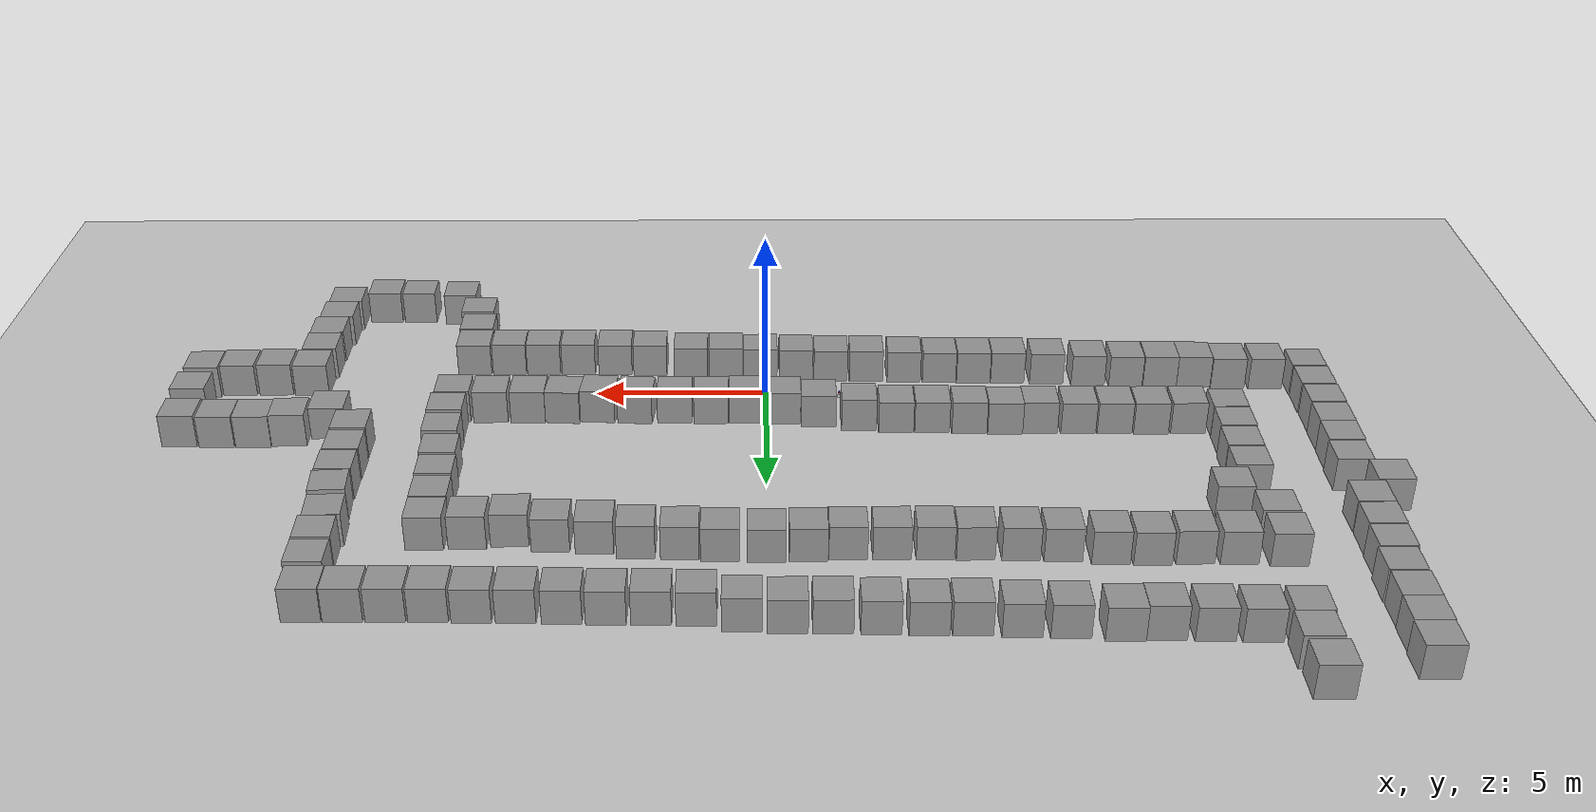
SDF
<sdf version="1.7">
 <world name="default">
  <light name="sun" type="directional">
   <pose>0 0 10 0 -0 0</pose>
   <diffuse>0.8 0.8 0.8 1</diffuse>
   <specular>0.2 0.2 0.2 1</specular>
   <attenuation>
    <range>1000</range>
    <constant>0.9</constant>
    <linear>0.01</linear>
    <quadratic>0.001</quadratic>
   </attenuation>
   <direction>-0.5 0.1 -0.9</direction>
   <spot><inner_angle>0</inner_angle><outer_angle>0</outer_angle><falloff>0</falloff></spot>
  </light>
  <model name="ground_plane">
   <static>1</static>
   <link name="link">
    <collision name="collision">
     <geometry><plane><normal>0 0 1</normal><size>100 100</size></plane></geometry>
     <surface><friction><ode><mu>100</mu><mu2>50</mu2></ode></friction></surface>
    </collision>
    <visual name="visual">
     <cast_shadows>0</cast_shadows>
     <geometry><plane><normal>0 0 1</normal><size>100 100</size></plane></geometry>
     <material>
      <script><uri>file://media/materials/scripts/gazebo.material</uri><name>Gazebo/Grey</name></script>
     </material>
    </visual>
   </link>
  </model>
  <gravity>0 0 -9.8</gravity>
  <magnetic_field>6e-06 2.3e-05 -4.2e-05</magnetic_field>
  <atmosphere type="adiabatic"/>
  <physics type="ode">
   <max_step_size>0.001</max_step_size>
   <real_time_factor>1</real_time_factor>
   <real_time_update_rate>1000</real_time_update_rate>
  </physics>
  <scene><ambient>0.4 0.4 0.4 1</ambient><background>0.7 0.7 0.7 1</background><shadows>1</shadows></scene>
  <audio><device>default</device></audio>
  <spherical_coordinates>
   <surface_model>EARTH_WGS84</surface_model>
   <latitude_deg>0</latitude_deg>
   <longitude_deg>0</longitude_deg>
   <elevation>0</elevation>
   <heading_deg>0</heading_deg>
  </spherical_coordinates>
  <model name="my_bot">
   <link name="base_link">
    <inertial>
     <pose>0.177215 0 0.060506 0 -0 0</pose>
     <mass>0.79</mass>
     <inertia>
      <ixx>0.00271819</ixx>
      <ixy>0</ixy>
      <ixz>0.000910886</ixz>
      <iyy>0.0116814</iyy>
      <iyz>0</iyz>
      <izz>0.011264</izz>
     </inertia>
    </inertial>
    <collision name="base_link_fixed_joint_lump__chassis_collision">
     <pose>0.12 0 0.05 0 -0 0</pose>
     <geometry><box><size>0.24 0.16 0.1</size></box></geometry>
    </collision>
    <collision name="base_link_fixed_joint_lump__caster_wheel_collision_1">
     <pose>0.24 0 0 0 -0 0</pose>
     <geometry><sphere><radius>0.04</radius></sphere></geometry>
     <surface><friction><ode><mu>0.001</mu><mu2>0.001</mu2></ode></friction></surface>
    </collision>
    <collision name="base_link_fixed_joint_lump__laser_frame_collision_2">
     <pose>0.2 0 0.12 0 -0 0</pose>
     <geometry><cylinder><length>0.04</length><radius>0.033</radius></cylinder></geometry>
    </collision>
    <visual name="base_link_fixed_joint_lump__chassis_visual">
     <pose>0.12 0 0.05 0 -0 0</pose>
     <geometry><box><size>0.24 0.2 0.1</size></box></geometry>
     <material>
      <script><name>Gazebo/White</name><uri>file://media/materials/scripts/gazebo.material</uri></script>
     </material>
    </visual>
    <visual name="base_link_fixed_joint_lump__camera_link_visual_1">
     <pose>0.2 0 0.16 0 -0 0</pose>
     <geometry><box><size>0.025 0.09 0.02</size></box></geometry>
     <material>
      <script><name>Gazebo/Blue</name><uri>file://media/materials/scripts/gazebo.material</uri></script>
     </material>
    </visual>
    <visual name="base_link_fixed_joint_lump__caster_wheel_visual_2">
     <pose>0.24 0 0 0 -0 0</pose>
     <geometry><sphere><radius>0.04</radius></sphere></geometry>
     <material>
      <script><name>Gazebo/Black</name><uri>file://media/materials/scripts/gazebo.material</uri></script>
     </material>
    </visual>
    <visual name="base_link_fixed_joint_lump__laser_frame_visual_3">
     <pose>0.2 0 0.12 0 -0 0</pose>
     <geometry><cylinder><length>0.04</length><radius>0.033</radius></cylinder></geometry>
     <material>
      <script><name>Gazebo/Red</name><uri>file://media/materials/scripts/gazebo.material</uri></script>
     </material>
    </visual>
    <sensor name="camera" type="depth">
     <visualize>1</visualize>
     <update_rate>10</update_rate>
     <camera>
      <horizontal_fov>1.089</horizontal_fov>
      <image><format>B8G8R8</format><width>640</width><height>480</height></image>
      <clip><near>0.05</near><far>8</far></clip>
     </camera>
     <plugin name="camera_controller" filename="libgazebo_ros_camera.so">
      <frame_name>camera_link_optical</frame_name>
      <min_depth>0.1</min_depth>
      <max_depth>100.0</max_depth>
     </plugin>
     <pose>0.2 0 0.16 0 -0 0</pose>
    </sensor>
    <sensor name="laser" type="ray">
     <visualize>1</visualize>
     <update_rate>10</update_rate>
     <ray>
      <scan>
       <horizontal>
        <samples>360</samples>
        <min_angle>-3.14</min_angle>
        <max_angle>3.14</max_angle>
        <resolution>1</resolution>
       </horizontal>
       <vertical><samples>1</samples><min_angle>0</min_angle><max_angle>0</max_angle></vertical>
      </scan>
      <range><min>0.3</min><max>12</max></range>
     </ray>
     <plugin name="laser_controller" filename="libgazebo_ros_ray_sensor.so">
      <ros><argument>~/out:=scan</argument></ros>
      <output_type>sensor_msgs/LaserScan</output_type>
      <frame_name>laser_frame</frame_name>
     </plugin>
     <pose>0.2 0 0.12 0 -0 0</pose>
    </sensor>
   </link>
   <joint name="left_wheel_joint" type="revolute">
    <pose relative_to="base_link">0 0.1 0 -1.5708 0 0</pose>
    <parent>base_link</parent>
    <child>left_wheel</child>
    <axis>
     <xyz>0 0 1</xyz>
     <limit><lower>-1e+16</lower><upper>1e+16</upper></limit>
     <dynamics><spring_reference>0</spring_reference><spring_stiffness>0</spring_stiffness></dynamics>
    </axis>
   </joint>
   <link name="left_wheel">
    <pose relative_to="left_wheel_joint">0 0 0 0 -0 0</pose>
    <inertial>
     <mass>0.1</mass>
     <inertia>
      <ixx>5.33333e-05</ixx>
      <ixy>0</ixy>
      <ixz>0</ixz>
      <iyy>5.33333e-05</iyy>
      <iyz>0</iyz>
      <izz>8e-05</izz>
     </inertia>
    </inertial>
    <collision name="left_wheel_collision"><geometry><sphere><radius>0.04</radius></sphere></geometry></collision>
    <visual name="left_wheel_visual">
     <geometry><cylinder><length>0.04</length><radius>0.04</radius></cylinder></geometry>
     <material>
      <script><name>Gazebo/Blue</name><uri>file://media/materials/scripts/gazebo.material</uri></script>
     </material>
    </visual>
   </link>
   <joint name="right_wheel_joint" type="revolute">
    <pose relative_to="base_link">0 -0.1 0 1.5708 -0 0</pose>
    <parent>base_link</parent>
    <child>right_wheel</child>
    <axis>
     <xyz>0 0 -1</xyz>
     <limit><lower>-1e+16</lower><upper>1e+16</upper></limit>
     <dynamics><spring_reference>0</spring_reference><spring_stiffness>0</spring_stiffness></dynamics>
    </axis>
   </joint>
   <link name="right_wheel">
    <pose relative_to="right_wheel_joint">0 0 0 0 -0 0</pose>
    <inertial>
     <mass>0.1</mass>
     <inertia>
      <ixx>5.33333e-05</ixx>
      <ixy>0</ixy>
      <ixz>0</ixz>
      <iyy>5.33333e-05</iyy>
      <iyz>0</iyz>
      <izz>8e-05</izz>
     </inertia>
    </inertial>
    <collision name="right_wheel_collision">
     <geometry><sphere><radius>0.04</radius></sphere></geometry>
    </collision>
    <visual name="right_wheel_visual">
     <geometry><cylinder><length>0.04</length><radius>0.04</radius></cylinder></geometry>
     <material>
      <script><name>Gazebo/Blue</name><uri>file://media/materials/scripts/gazebo.material</uri></script>
     </material>
    </visual>
   </link>
   <static>0</static>
   <plugin name="gazebo_ros2_control" filename="libgazebo_ros2_control.so">
    <parameters>/home/ivan/dev_ws/install/my_bot/share/my_bot/config/my_controllers.yaml</parameters>
   </plugin>
   <pose>-2.37462 0.266413 0.039999 -1.4e-05 -6e-06 -0.175538</pose>
  </model>
  <model name="unit_box">
   <pose>0.555507 1.19168 0.499995 0 1e-05 0</pose>
   <link name="link">
    <inertial>
     <mass>1</mass>
     <inertia>
      <ixx>0.166667</ixx>
      <ixy>0</ixy>
      <ixz>0</ixz>
      <iyy>0.166667</iyy>
      <iyz>0</iyz>
      <izz>0.166667</izz>
     </inertia>
    </inertial>
    <collision name="collision"><geometry><box><size>1 1 1</size></box></geometry></collision>
    <visual name="visual">
     <geometry><box><size>1 1 1</size></box></geometry>
     <material>
      <script><name>Gazebo/Grey</name><uri>file://media/materials/scripts/gazebo.material</uri></script>
     </material>
    </visual>
   </link>
  </model>
  <model name="unit_box_0">
   <pose>1.57825 1.23788 0.499995 0 -1e-05 0</pose>
   <link name="link">
    <inertial>
     <mass>1</mass>
     <inertia>
      <ixx>0.166667</ixx>
      <ixy>0</ixy>
      <ixz>0</ixz>
      <iyy>0.166667</iyy>
      <iyz>0</iyz>
      <izz>0.166667</izz>
     </inertia>
    </inertial>
    <collision name="collision"><geometry><box><size>1 1 1</size></box></geometry></collision>
    <visual name="visual">
     <geometry><box><size>1 1 1</size></box></geometry>
     <material>
      <script><name>Gazebo/Grey</name><uri>file://media/materials/scripts/gazebo.material</uri></script>
     </material>
    </visual>
   </link>
  </model>
  <model name="unit_box_1">
   <pose>2.63146 1.21638 0.499995 0 1e-05 0</pose>
   <link name="link">
    <inertial>
     <mass>1</mass>
     <inertia>
      <ixx>0.166667</ixx>
      <ixy>0</ixy>
      <ixz>0</ixz>
      <iyy>0.166667</iyy>
      <iyz>0</iyz>
      <izz>0.166667</izz>
     </inertia>
    </inertial>
    <collision name="collision"><geometry><box><size>1 1 1</size></box></geometry></collision>
    <visual name="visual">
     <geometry><box><size>1 1 1</size></box></geometry>
     <material>
      <script><name>Gazebo/Grey</name><uri>file://media/materials/scripts/gazebo.material</uri></script>
     </material>
    </visual>
   </link>
  </model>
  <model name="unit_box_2">
   <pose>3.74606 1.22705 0.499995 -1e-05 -0 -0.082022</pose>
   <link name="link">
    <inertial>
     <mass>1</mass>
     <inertia>
      <ixx>0.166667</ixx>
      <ixy>0</ixy>
      <ixz>0</ixz>
      <iyy>0.166667</iyy>
      <iyz>0</iyz>
      <izz>0.166667</izz>
     </inertia>
    </inertial>
    <collision name="collision"><geometry><box><size>1 1 1</size></box></geometry></collision>
    <visual name="visual">
     <geometry><box><size>1 1 1</size></box></geometry>
     <material>
      <script><name>Gazebo/Grey</name><uri>file://media/materials/scripts/gazebo.material</uri></script>
     </material>
    </visual>
   </link>
  </model>
  <model name="unit_box_3">
   <pose>4.82643 1.14872 0.499995 -1e-05 0 -0.080673</pose>
   <link name="link">
    <inertial>
     <mass>1</mass>
     <inertia>
      <ixx>0.166667</ixx>
      <ixy>0</ixy>
      <ixz>0</ixz>
      <iyy>0.166667</iyy>
      <iyz>0</iyz>
      <izz>0.166667</izz>
     </inertia>
    </inertial>
    <collision name="collision"><geometry><box><size>1 1 1</size></box></geometry></collision>
    <visual name="visual">
     <geometry><box><size>1 1 1</size></box></geometry>
     <material>
      <script><name>Gazebo/Grey</name><uri>file://media/materials/scripts/gazebo.material</uri></script>
     </material>
    </visual>
   </link>
  </model>
  <model name="unit_box_4">
   <pose>5.83439 1.19515 0.499995 -1e-05 -0 -0.078203</pose>
   <link name="link">
    <inertial>
     <mass>1</mass>
     <inertia>
      <ixx>0.166667</ixx>
      <ixy>0</ixy>
      <ixz>0</ixz>
      <iyy>0.166667</iyy>
      <iyz>0</iyz>
      <izz>0.166667</izz>
     </inertia>
    </inertial>
    <collision name="collision"><geometry><box><size>1 1 1</size></box></geometry></collision>
    <visual name="visual">
     <geometry><box><size>1 1 1</size></box></geometry>
     <material>
      <script><name>Gazebo/Grey</name><uri>file://media/materials/scripts/gazebo.material</uri></script>
     </material>
    </visual>
   </link>
  </model>
  <model name="unit_box_5">
   <pose>6.86221 1.16701 0.499995 -1e-05 -0 -0.020162</pose>
   <link name="link">
    <inertial>
     <mass>1</mass>
     <inertia>
      <ixx>0.166667</ixx>
      <ixy>0</ixy>
      <ixz>0</ixz>
      <iyy>0.166667</iyy>
      <iyz>0</iyz>
      <izz>0.166667</izz>
     </inertia>
    </inertial>
    <collision name="collision"><geometry><box><size>1 1 1</size></box></geometry></collision>
    <visual name="visual">
     <geometry><box><size>1 1 1</size></box></geometry>
     <material>
      <script><name>Gazebo/Grey</name><uri>file://media/materials/scripts/gazebo.material</uri></script>
     </material>
    </visual>
   </link>
  </model>
  <model name="unit_box_6">
   <pose>7.9487 1.15327 0.499995 -1e-05 0 0</pose>
   <link name="link">
    <inertial>
     <mass>1</mass>
     <inertia>
      <ixx>0.166667</ixx>
      <ixy>0</ixy>
      <ixz>0</ixz>
      <iyy>0.166667</iyy>
      <iyz>0</iyz>
      <izz>0.166667</izz>
     </inertia>
    </inertial>
    <collision name="collision"><geometry><box><size>1 1 1</size></box></geometry></collision>
    <visual name="visual">
     <geometry><box><size>1 1 1</size></box></geometry>
     <material>
      <script><name>Gazebo/Grey</name><uri>file://media/materials/scripts/gazebo.material</uri></script>
     </material>
    </visual>
   </link>
  </model>
  <model name="unit_box_7">
   <pose>9.03135 1.11313 0.499995 0 1e-05 0</pose>
   <link name="link">
    <inertial>
     <mass>1</mass>
     <inertia>
      <ixx>0.166667</ixx>
      <ixy>0</ixy>
      <ixz>0</ixz>
      <iyy>0.166667</iyy>
      <iyz>0</iyz>
      <izz>0.166667</izz>
     </inertia>
    </inertial>
    <collision name="collision"><geometry><box><size>1 1 1</size></box></geometry></collision>
    <visual name="visual">
     <geometry><box><size>1 1 1</size></box></geometry>
     <material>
      <script><name>Gazebo/Grey</name><uri>file://media/materials/scripts/gazebo.material</uri></script>
     </material>
    </visual>
   </link>
  </model>
  <model name="unit_box_8">
   <pose>8.76045 -1.66109 0.499995 0 -1e-05 0</pose>
   <link name="link">
    <inertial>
     <mass>1</mass>
     <inertia>
      <ixx>0.166667</ixx>
      <ixy>0</ixy>
      <ixz>0</ixz>
      <iyy>0.166667</iyy>
      <iyz>0</iyz>
      <izz>0.166667</izz>
     </inertia>
    </inertial>
    <collision name="collision"><geometry><box><size>1 1 1</size></box></geometry></collision>
    <visual name="visual">
     <geometry><box><size>1 1 1</size></box></geometry>
     <material>
      <script><name>Gazebo/Grey</name><uri>file://media/materials/scripts/gazebo.material</uri></script>
     </material>
    </visual>
   </link>
  </model>
  <model name="unit_box_9">
   <pose>7.71543 -1.67512 0.499995 0 1e-05 0</pose>
   <link name="link">
    <inertial>
     <mass>1</mass>
     <inertia>
      <ixx>0.166667</ixx>
      <ixy>0</ixy>
      <ixz>0</ixz>
      <iyy>0.166667</iyy>
      <iyz>0</iyz>
      <izz>0.166667</izz>
     </inertia>
    </inertial>
    <collision name="collision"><geometry><box><size>1 1 1</size></box></geometry></collision>
    <visual name="visual">
     <geometry><box><size>1 1 1</size></box></geometry>
     <material>
      <script><name>Gazebo/Grey</name><uri>file://media/materials/scripts/gazebo.material</uri></script>
     </material>
    </visual>
   </link>
  </model>
  <model name="unit_box_10">
   <pose>6.68845 -1.68927 0.499995 -1e-05 0 0</pose>
   <link name="link">
    <inertial>
     <mass>1</mass>
     <inertia>
      <ixx>0.166667</ixx>
      <ixy>0</ixy>
      <ixz>0</ixz>
      <iyy>0.166667</iyy>
      <iyz>0</iyz>
      <izz>0.166667</izz>
     </inertia>
    </inertial>
    <collision name="collision"><geometry><box><size>1 1 1</size></box></geometry></collision>
    <visual name="visual">
     <geometry><box><size>1 1 1</size></box></geometry>
     <material>
      <script><name>Gazebo/Grey</name><uri>file://media/materials/scripts/gazebo.material</uri></script>
     </material>
    </visual>
   </link>
  </model>
  <model name="unit_box_11">
   <pose>5.63972 -1.68978 0.499995 0 1e-05 0</pose>
   <link name="link">
    <inertial>
     <mass>1</mass>
     <inertia>
      <ixx>0.166667</ixx>
      <ixy>0</ixy>
      <ixz>0</ixz>
      <iyy>0.166667</iyy>
      <iyz>0</iyz>
      <izz>0.166667</izz>
     </inertia>
    </inertial>
    <collision name="collision"><geometry><box><size>1 1 1</size></box></geometry></collision>
    <visual name="visual">
     <geometry><box><size>1 1 1</size></box></geometry>
     <material>
      <script><name>Gazebo/Grey</name><uri>file://media/materials/scripts/gazebo.material</uri></script>
     </material>
    </visual>
   </link>
  </model>
  <model name="unit_box_12">
   <pose>4.52806 -1.6504 0.499995 -1e-05 0 0</pose>
   <link name="link">
    <inertial>
     <mass>1</mass>
     <inertia>
      <ixx>0.166667</ixx>
      <ixy>0</ixy>
      <ixz>0</ixz>
      <iyy>0.166667</iyy>
      <iyz>0</iyz>
      <izz>0.166667</izz>
     </inertia>
    </inertial>
    <collision name="collision"><geometry><box><size>1 1 1</size></box></geometry></collision>
    <visual name="visual">
     <geometry><box><size>1 1 1</size></box></geometry>
     <material>
      <script><name>Gazebo/Grey</name><uri>file://media/materials/scripts/gazebo.material</uri></script>
     </material>
    </visual>
   </link>
  </model>
  <model name="unit_box_13">
   <pose>3.47624 -1.6198 0.499995 0 1e-05 0</pose>
   <link name="link">
    <inertial>
     <mass>1</mass>
     <inertia>
      <ixx>0.166667</ixx>
      <ixy>0</ixy>
      <ixz>0</ixz>
      <iyy>0.166667</iyy>
      <iyz>0</iyz>
      <izz>0.166667</izz>
     </inertia>
    </inertial>
    <collision name="collision"><geometry><box><size>1 1 1</size></box></geometry></collision>
    <visual name="visual">
     <geometry><box><size>1 1 1</size></box></geometry>
     <material>
      <script><name>Gazebo/Grey</name><uri>file://media/materials/scripts/gazebo.material</uri></script>
     </material>
    </visual>
   </link>
  </model>
  <model name="unit_box_14">
   <pose>2.2423 -1.45852 0.499995 0 -1e-05 0</pose>
   <link name="link">
    <inertial>
     <mass>1</mass>
     <inertia>
      <ixx>0.166667</ixx>
      <ixy>0</ixy>
      <ixz>0</ixz>
      <iyy>0.166667</iyy>
      <iyz>0</iyz>
      <izz>0.166667</izz>
     </inertia>
    </inertial>
    <collision name="collision"><geometry><box><size>1 1 1</size></box></geometry></collision>
    <visual name="visual">
     <geometry><box><size>1 1 1</size></box></geometry>
     <material>
      <script><name>Gazebo/Grey</name><uri>file://media/materials/scripts/gazebo.material</uri></script>
     </material>
    </visual>
   </link>
  </model>
  <model name="unit_box_15">
   <pose>1.19901 -1.44068 0.5 -0 -0 -0</pose>
   <link name="link">
    <inertial>
     <mass>1</mass>
     <inertia>
      <ixx>0.166667</ixx>
      <ixy>0</ixy>
      <ixz>0</ixz>
      <iyy>0.166667</iyy>
      <iyz>0</iyz>
      <izz>0.166667</izz>
     </inertia>
    </inertial>
    <collision name="collision"><geometry><box><size>1 1 1</size></box></geometry></collision>
    <visual name="visual">
     <geometry><box><size>1 1 1</size></box></geometry>
     <material>
      <script><name>Gazebo/Grey</name><uri>file://media/materials/scripts/gazebo.material</uri></script>
     </material>
    </visual>
   </link>
  </model>
  <model name="unit_box_16">
   <pose>8.79403 -2.72072 0.499995 -1e-05 0 0</pose>
   <link name="link">
    <inertial>
     <mass>1</mass>
     <inertia>
      <ixx>0.166667</ixx>
      <ixy>0</ixy>
      <ixz>0</ixz>
      <iyy>0.166667</iyy>
      <iyz>0</iyz>
      <izz>0.166667</izz>
     </inertia>
    </inertial>
    <collision name="collision"><geometry><box><size>1 1 1</size></box></geometry></collision>
    <visual name="visual">
     <geometry><box><size>1 1 1</size></box></geometry>
     <material>
      <script><name>Gazebo/Grey</name><uri>file://media/materials/scripts/gazebo.material</uri></script>
     </material>
    </visual>
   </link>
  </model>
  <model name="unit_box_17">
   <pose>8.89804 -3.86534 0.499995 0 1e-05 0</pose>
   <link name="link">
    <inertial>
     <mass>1</mass>
     <inertia>
      <ixx>0.166667</ixx>
      <ixy>0</ixy>
      <ixz>0</ixz>
      <iyy>0.166667</iyy>
      <iyz>0</iyz>
      <izz>0.166667</izz>
     </inertia>
    </inertial>
    <collision name="collision"><geometry><box><size>1 1 1</size></box></geometry></collision>
    <visual name="visual">
     <geometry><box><size>1 1 1</size></box></geometry>
     <material>
      <script><name>Gazebo/Grey</name><uri>file://media/materials/scripts/gazebo.material</uri></script>
     </material>
    </visual>
   </link>
  </model>
  <model name="unit_box_18">
   <pose>9.59968 -4.97217 0.499995 -1e-05 0 0</pose>
   <link name="link">
    <inertial>
     <mass>1</mass>
     <inertia>
      <ixx>0.166667</ixx>
      <ixy>0</ixy>
      <ixz>0</ixz>
      <iyy>0.166667</iyy>
      <iyz>0</iyz>
      <izz>0.166667</izz>
     </inertia>
    </inertial>
    <collision name="collision"><geometry><box><size>1 1 1</size></box></geometry></collision>
    <visual name="visual">
     <geometry><box><size>1 1 1</size></box></geometry>
     <material>
      <script><name>Gazebo/Grey</name><uri>file://media/materials/scripts/gazebo.material</uri></script>
     </material>
    </visual>
   </link>
  </model>
  <model name="unit_box_19">
   <pose>10.916 -5.08427 0.499995 0 1e-05 0</pose>
   <link name="link">
    <inertial>
     <mass>1</mass>
     <inertia>
      <ixx>0.166667</ixx>
      <ixy>0</ixy>
      <ixz>0</ixz>
      <iyy>0.166667</iyy>
      <iyz>0</iyz>
      <izz>0.166667</izz>
     </inertia>
    </inertial>
    <collision name="collision"><geometry><box><size>1 1 1</size></box></geometry></collision>
    <visual name="visual">
     <geometry><box><size>1 1 1</size></box></geometry>
     <material>
      <script><name>Gazebo/Grey</name><uri>file://media/materials/scripts/gazebo.material</uri></script>
     </material>
    </visual>
   </link>
  </model>
  <model name="unit_box_20">
   <pose>11.9942 -5.11768 0.499995 -1e-05 0 0</pose>
   <link name="link">
    <inertial>
     <mass>1</mass>
     <inertia>
      <ixx>0.166667</ixx>
      <ixy>0</ixy>
      <ixz>0</ixz>
      <iyy>0.166667</iyy>
      <iyz>0</iyz>
      <izz>0.166667</izz>
     </inertia>
    </inertial>
    <collision name="collision"><geometry><box><size>1 1 1</size></box></geometry></collision>
    <visual name="visual">
     <geometry><box><size>1 1 1</size></box></geometry>
     <material>
      <script><name>Gazebo/Grey</name><uri>file://media/materials/scripts/gazebo.material</uri></script>
     </material>
    </visual>
   </link>
  </model>
  <model name="unit_box_21">
   <pose>13.128 -4.61853 0.499995 0 1e-05 0</pose>
   <link name="link">
    <inertial>
     <mass>1</mass>
     <inertia>
      <ixx>0.166667</ixx>
      <ixy>0</ixy>
      <ixz>0</ixz>
      <iyy>0.166667</iyy>
      <iyz>0</iyz>
      <izz>0.166667</izz>
     </inertia>
    </inertial>
    <collision name="collision"><geometry><box><size>1 1 1</size></box></geometry></collision>
    <visual name="visual">
     <geometry><box><size>1 1 1</size></box></geometry>
     <material>
      <script><name>Gazebo/Grey</name><uri>file://media/materials/scripts/gazebo.material</uri></script>
     </material>
    </visual>
   </link>
  </model>
  <model name="unit_box_22">
   <pose>13.2109 -3.58644 0.499995 -1e-05 0 0</pose>
   <link name="link">
    <inertial>
     <mass>1</mass>
     <inertia>
      <ixx>0.166667</ixx>
      <ixy>0</ixy>
      <ixz>0</ixz>
      <iyy>0.166667</iyy>
      <iyz>0</iyz>
      <izz>0.166667</izz>
     </inertia>
    </inertial>
    <collision name="collision"><geometry><box><size>1 1 1</size></box></geometry></collision>
    <visual name="visual">
     <geometry><box><size>1 1 1</size></box></geometry>
     <material>
      <script><name>Gazebo/Grey</name><uri>file://media/materials/scripts/gazebo.material</uri></script>
     </material>
    </visual>
   </link>
  </model>
  <model name="unit_box_23">
   <pose>13.3131 -2.54327 0.499995 0 1e-05 0</pose>
   <link name="link">
    <inertial>
     <mass>1</mass>
     <inertia>
      <ixx>0.166667</ixx>
      <ixy>0</ixy>
      <ixz>0</ixz>
      <iyy>0.166667</iyy>
      <iyz>0</iyz>
      <izz>0.166667</izz>
     </inertia>
    </inertial>
    <collision name="collision"><geometry><box><size>1 1 1</size></box></geometry></collision>
    <visual name="visual">
     <geometry><box><size>1 1 1</size></box></geometry>
     <material>
      <script><name>Gazebo/Grey</name><uri>file://media/materials/scripts/gazebo.material</uri></script>
     </material>
    </visual>
   </link>
  </model>
  <model name="unit_box_24">
   <pose>13.3431 -1.50286 0.499995 -1e-05 0 0</pose>
   <link name="link">
    <inertial>
     <mass>1</mass>
     <inertia>
      <ixx>0.166667</ixx>
      <ixy>0</ixy>
      <ixz>0</ixz>
      <iyy>0.166667</iyy>
      <iyz>0</iyz>
      <izz>0.166667</izz>
     </inertia>
    </inertial>
    <collision name="collision"><geometry><box><size>1 1 1</size></box></geometry></collision>
    <visual name="visual">
     <geometry><box><size>1 1 1</size></box></geometry>
     <material>
      <script><name>Gazebo/Grey</name><uri>file://media/materials/scripts/gazebo.material</uri></script>
     </material>
    </visual>
   </link>
  </model>
  <model name="unit_box_25">
   <pose>13.4227 -0.430542 0.499995 0 1e-05 0</pose>
   <link name="link">
    <inertial>
     <mass>1</mass>
     <inertia>
      <ixx>0.166667</ixx>
      <ixy>0</ixy>
      <ixz>0</ixz>
      <iyy>0.166667</iyy>
      <iyz>0</iyz>
      <izz>0.166667</izz>
     </inertia>
    </inertial>
    <collision name="collision"><geometry><box><size>1 1 1</size></box></geometry></collision>
    <visual name="visual">
     <geometry><box><size>1 1 1</size></box></geometry>
     <material>
      <script><name>Gazebo/Grey</name><uri>file://media/materials/scripts/gazebo.material</uri></script>
     </material>
    </visual>
   </link>
  </model>
  <model name="unit_box_26">
   <pose>14.4911 -0.475819 0.499995 -1e-05 0 0</pose>
   <link name="link">
    <inertial>
     <mass>1</mass>
     <inertia>
      <ixx>0.166667</ixx>
      <ixy>0</ixy>
      <ixz>0</ixz>
      <iyy>0.166667</iyy>
      <iyz>0</iyz>
      <izz>0.166667</izz>
     </inertia>
    </inertial>
    <collision name="collision"><geometry><box><size>1 1 1</size></box></geometry></collision>
    <visual name="visual">
     <geometry><box><size>1 1 1</size></box></geometry>
     <material>
      <script><name>Gazebo/Grey</name><uri>file://media/materials/scripts/gazebo.material</uri></script>
     </material>
    </visual>
   </link>
  </model>
  <model name="unit_box_27">
   <pose>15.5576 -0.45019 0.499995 0 1e-05 0</pose>
   <link name="link">
    <inertial>
     <mass>1</mass>
     <inertia>
      <ixx>0.166667</ixx>
      <ixy>0</ixy>
      <ixz>0</ixz>
      <iyy>0.166667</iyy>
      <iyz>0</iyz>
      <izz>0.166667</izz>
     </inertia>
    </inertial>
    <collision name="collision"><geometry><box><size>1 1 1</size></box></geometry></collision>
    <visual name="visual">
     <geometry><box><size>1 1 1</size></box></geometry>
     <material>
      <script><name>Gazebo/Grey</name><uri>file://media/materials/scripts/gazebo.material</uri></script>
     </material>
    </visual>
   </link>
  </model>
  <model name="unit_box_28">
   <pose>16.5913 -0.356361 0.499995 -1e-05 0 0</pose>
   <link name="link">
    <inertial>
     <mass>1</mass>
     <inertia>
      <ixx>0.166667</ixx>
      <ixy>0</ixy>
      <ixz>0</ixz>
      <iyy>0.166667</iyy>
      <iyz>0</iyz>
      <izz>0.166667</izz>
     </inertia>
    </inertial>
    <collision name="collision"><geometry><box><size>1 1 1</size></box></geometry></collision>
    <visual name="visual">
     <geometry><box><size>1 1 1</size></box></geometry>
     <material>
      <script><name>Gazebo/Grey</name><uri>file://media/materials/scripts/gazebo.material</uri></script>
     </material>
    </visual>
   </link>
  </model>
  <model name="unit_box_29">
   <pose>14.5156 2.51049 0.499995 -0 -1e-05 0.030671</pose>
   <link name="link">
    <inertial>
     <mass>1</mass>
     <inertia>
      <ixx>0.166667</ixx>
      <ixy>0</ixy>
      <ixz>0</ixz>
      <iyy>0.166667</iyy>
      <iyz>0</iyz>
      <izz>0.166667</izz>
     </inertia>
    </inertial>
    <collision name="collision"><geometry><box><size>1 1 1</size></box></geometry></collision>
    <visual name="visual">
     <geometry><box><size>1 1 1</size></box></geometry>
     <material>
      <script><name>Gazebo/Grey</name><uri>file://media/materials/scripts/gazebo.material</uri></script>
     </material>
    </visual>
   </link>
  </model>
  <model name="unit_box_30">
   <pose>11.6391 3.0877 0.499995 1e-05 -0 0</pose>
   <link name="link">
    <inertial>
     <mass>1</mass>
     <inertia>
      <ixx>0.166667</ixx>
      <ixy>0</ixy>
      <ixz>0</ixz>
      <iyy>0.166667</iyy>
      <iyz>0</iyz>
      <izz>0.166667</izz>
     </inertia>
    </inertial>
    <collision name="collision"><geometry><box><size>1 1 1</size></box></geometry></collision>
    <visual name="visual">
     <geometry><box><size>1 1 1</size></box></geometry>
     <material>
      <script><name>Gazebo/Grey</name><uri>file://media/materials/scripts/gazebo.material</uri></script>
     </material>
    </visual>
   </link>
  </model>
  <model name="unit_box_31">
   <pose>15.533 2.52411 0.499995 -1e-05 0 0</pose>
   <link name="link">
    <inertial>
     <mass>1</mass>
     <inertia>
      <ixx>0.166667</ixx>
      <ixy>0</ixy>
      <ixz>0</ixz>
      <iyy>0.166667</iyy>
      <iyz>0</iyz>
      <izz>0.166667</izz>
     </inertia>
    </inertial>
    <collision name="collision"><geometry><box><size>1 1 1</size></box></geometry></collision>
    <visual name="visual">
     <geometry><box><size>1 1 1</size></box></geometry>
     <material>
      <script><name>Gazebo/Grey</name><uri>file://media/materials/scripts/gazebo.material</uri></script>
     </material>
    </visual>
   </link>
  </model>
  <model name="unit_box_32">
   <pose>16.6003 2.46368 0.499995 0 1e-05 0</pose>
   <link name="link">
    <inertial>
     <mass>1</mass>
     <inertia>
      <ixx>0.166667</ixx>
      <ixy>0</ixy>
      <ixz>0</ixz>
      <iyy>0.166667</iyy>
      <iyz>0</iyz>
      <izz>0.166667</izz>
     </inertia>
    </inertial>
    <collision name="collision"><geometry><box><size>1 1 1</size></box></geometry></collision>
    <visual name="visual">
     <geometry><box><size>1 1 1</size></box></geometry>
     <material>
      <script><name>Gazebo/Grey</name><uri>file://media/materials/scripts/gazebo.material</uri></script>
     </material>
    </visual>
   </link>
  </model>
  <model name="unit_box_33">
   <pose>16.6668 0.917596 0.499995 -1e-05 0 0</pose>
   <link name="link">
    <inertial>
     <mass>1</mass>
     <inertia>
      <ixx>0.166667</ixx>
      <ixy>0</ixy>
      <ixz>0</ixz>
      <iyy>0.166667</iyy>
      <iyz>0</iyz>
      <izz>0.166667</izz>
     </inertia>
    </inertial>
    <collision name="collision"><geometry><box><size>1 1 1</size></box></geometry></collision>
    <visual name="visual">
     <geometry><box><size>1 1 1</size></box></geometry>
     <material>
      <script><name>Gazebo/Grey</name><uri>file://media/materials/scripts/gazebo.material</uri></script>
     </material>
    </visual>
   </link>
  </model>
  <model name="unit_box_34">
   <pose>11.6314 4.22803 0.499995 1e-05 -0 0</pose>
   <link name="link">
    <inertial>
     <mass>1</mass>
     <inertia>
      <ixx>0.166667</ixx>
      <ixy>0</ixy>
      <ixz>0</ixz>
      <iyy>0.166667</iyy>
      <iyz>0</iyz>
      <izz>0.166667</izz>
     </inertia>
    </inertial>
    <collision name="collision"><geometry><box><size>1 1 1</size></box></geometry></collision>
    <visual name="visual">
     <geometry><box><size>1 1 1</size></box></geometry>
     <material>
      <script><name>Gazebo/Grey</name><uri>file://media/materials/scripts/gazebo.material</uri></script>
     </material>
    </visual>
   </link>
  </model>
  <model name="unit_box_35">
   <pose>11.654 5.25725 0.499995 1e-05 -0 0.004424</pose>
   <link name="link">
    <inertial>
     <mass>1</mass>
     <inertia>
      <ixx>0.166667</ixx>
      <ixy>0</ixy>
      <ixz>0</ixz>
      <iyy>0.166667</iyy>
      <iyz>0</iyz>
      <izz>0.166667</izz>
     </inertia>
    </inertial>
    <collision name="collision"><geometry><box><size>1 1 1</size></box></geometry></collision>
    <visual name="visual">
     <geometry><box><size>1 1 1</size></box></geometry>
     <material>
      <script><name>Gazebo/Grey</name><uri>file://media/materials/scripts/gazebo.material</uri></script>
     </material>
    </visual>
   </link>
  </model>
  <model name="unit_box_36">
   <pose>13.5174 2.43423 0.499995 1e-05 0 0.030648</pose>
   <link name="link">
    <inertial>
     <mass>1</mass>
     <inertia>
      <ixx>0.166667</ixx>
      <ixy>0</ixy>
      <ixz>0</ixz>
      <iyy>0.166667</iyy>
      <iyz>0</iyz>
      <izz>0.166667</izz>
     </inertia>
    </inertial>
    <collision name="collision"><geometry><box><size>1 1 1</size></box></geometry></collision>
    <visual name="visual">
     <geometry><box><size>1 1 1</size></box></geometry>
     <material>
      <script><name>Gazebo/Grey</name><uri>file://media/materials/scripts/gazebo.material</uri></script>
     </material>
    </visual>
   </link>
  </model>
  <model name="unit_box_37">
   <pose>11.6462 6.2886 0.5 0 -0 0.069266</pose>
   <link name="link">
    <inertial>
     <mass>1</mass>
     <inertia>
      <ixx>0.166667</ixx>
      <ixy>0</ixy>
      <ixz>0</ixz>
      <iyy>0.166667</iyy>
      <iyz>0</iyz>
      <izz>0.166667</izz>
     </inertia>
    </inertial>
    <collision name="collision"><geometry><box><size>1 1 1</size></box></geometry></collision>
    <visual name="visual">
     <geometry><box><size>1 1 1</size></box></geometry>
     <material>
      <script><name>Gazebo/Grey</name><uri>file://media/materials/scripts/gazebo.material</uri></script>
     </material>
    </visual>
   </link>
  </model>
  <model name="unit_box_38">
   <pose>12.4601 2.0331 0.499995 -1e-05 0 0</pose>
   <link name="link">
    <inertial>
     <mass>1</mass>
     <inertia>
      <ixx>0.166667</ixx>
      <ixy>0</ixy>
      <ixz>0</ixz>
      <iyy>0.166667</iyy>
      <iyz>0</iyz>
      <izz>0.166667</izz>
     </inertia>
    </inertial>
    <collision name="collision"><geometry><box><size>1 1 1</size></box></geometry></collision>
    <visual name="visual">
     <geometry><box><size>1 1 1</size></box></geometry>
     <material>
      <script><name>Gazebo/Grey</name><uri>file://media/materials/scripts/gazebo.material</uri></script>
     </material>
    </visual>
   </link>
  </model>
  <model name="unit_box_39">
   <pose>9.10292 2.14493 0.499995 -1e-05 0 0</pose>
   <link name="link">
    <inertial>
     <mass>1</mass>
     <inertia>
      <ixx>0.166667</ixx>
      <ixy>0</ixy>
      <ixz>0</ixz>
      <iyy>0.166667</iyy>
      <iyz>0</iyz>
      <izz>0.166667</izz>
     </inertia>
    </inertial>
    <collision name="collision"><geometry><box><size>1 1 1</size></box></geometry></collision>
    <visual name="visual">
     <geometry><box><size>1 1 1</size></box></geometry>
     <material>
      <script><name>Gazebo/Grey</name><uri>file://media/materials/scripts/gazebo.material</uri></script>
     </material>
    </visual>
   </link>
  </model>
  <model name="unit_box_40">
   <pose>9.08102 3.26349 0.499995 0 1e-05 0</pose>
   <link name="link">
    <inertial>
     <mass>1</mass>
     <inertia>
      <ixx>0.166667</ixx>
      <ixy>0</ixy>
      <ixz>0</ixz>
      <iyy>0.166667</iyy>
      <iyz>0</iyz>
      <izz>0.166667</izz>
     </inertia>
    </inertial>
    <collision name="collision"><geometry><box><size>1 1 1</size></box></geometry></collision>
    <visual name="visual">
     <geometry><box><size>1 1 1</size></box></geometry>
     <material>
      <script><name>Gazebo/Grey</name><uri>file://media/materials/scripts/gazebo.material</uri></script>
     </material>
    </visual>
   </link>
  </model>
  <model name="unit_box_41">
   <pose>8.97202 4.41198 0.499995 -1e-05 0 0</pose>
   <link name="link">
    <inertial>
     <mass>1</mass>
     <inertia>
      <ixx>0.166667</ixx>
      <ixy>0</ixy>
      <ixz>0</ixz>
      <iyy>0.166667</iyy>
      <iyz>0</iyz>
      <izz>0.166667</izz>
     </inertia>
    </inertial>
    <collision name="collision"><geometry><box><size>1 1 1</size></box></geometry></collision>
    <visual name="visual">
     <geometry><box><size>1 1 1</size></box></geometry>
     <material>
      <script><name>Gazebo/Grey</name><uri>file://media/materials/scripts/gazebo.material</uri></script>
     </material>
    </visual>
   </link>
  </model>
  <model name="unit_box_42">
   <pose>8.92411 5.50557 0.499995 0 1e-05 0</pose>
   <link name="link">
    <inertial>
     <mass>1</mass>
     <inertia>
      <ixx>0.166667</ixx>
      <ixy>0</ixy>
      <ixz>0</ixz>
      <iyy>0.166667</iyy>
      <iyz>0</iyz>
      <izz>0.166667</izz>
     </inertia>
    </inertial>
    <collision name="collision"><geometry><box><size>1 1 1</size></box></geometry></collision>
    <visual name="visual">
     <geometry><box><size>1 1 1</size></box></geometry>
     <material>
      <script><name>Gazebo/Grey</name><uri>file://media/materials/scripts/gazebo.material</uri></script>
     </material>
    </visual>
   </link>
  </model>
  <model name="unit_box_43">
   <pose>8.90039 6.60086 0.499995 -1e-05 0 0</pose>
   <link name="link">
    <inertial>
     <mass>1</mass>
     <inertia>
      <ixx>0.166667</ixx>
      <ixy>0</ixy>
      <ixz>0</ixz>
      <iyy>0.166667</iyy>
      <iyz>0</iyz>
      <izz>0.166667</izz>
     </inertia>
    </inertial>
    <collision name="collision"><geometry><box><size>1 1 1</size></box></geometry></collision>
    <visual name="visual">
     <geometry><box><size>1 1 1</size></box></geometry>
     <material>
      <script><name>Gazebo/Grey</name><uri>file://media/materials/scripts/gazebo.material</uri></script>
     </material>
    </visual>
   </link>
  </model>
  <model name="unit_box_44">
   <pose>8.89491 7.65407 0.499995 0 1e-05 0</pose>
   <link name="link">
    <inertial>
     <mass>1</mass>
     <inertia>
      <ixx>0.166667</ixx>
      <ixy>0</ixy>
      <ixz>0</ixz>
      <iyy>0.166667</iyy>
      <iyz>0</iyz>
      <izz>0.166667</izz>
     </inertia>
    </inertial>
    <collision name="collision"><geometry><box><size>1 1 1</size></box></geometry></collision>
    <visual name="visual">
     <geometry><box><size>1 1 1</size></box></geometry>
     <material>
      <script><name>Gazebo/Grey</name><uri>file://media/materials/scripts/gazebo.material</uri></script>
     </material>
    </visual>
   </link>
  </model>
  <model name="unit_box_45">
   <pose>11.54 7.48372 0.499995 -1e-05 -0 0.048086</pose>
   <link name="link">
    <inertial>
     <mass>1</mass>
     <inertia>
      <ixx>0.166667</ixx>
      <ixy>0</ixy>
      <ixz>0</ixz>
      <iyy>0.166667</iyy>
      <iyz>0</iyz>
      <izz>0.166667</izz>
     </inertia>
    </inertial>
    <collision name="collision"><geometry><box><size>1 1 1</size></box></geometry></collision>
    <visual name="visual">
     <geometry><box><size>1 1 1</size></box></geometry>
     <material>
      <script><name>Gazebo/Grey</name><uri>file://media/materials/scripts/gazebo.material</uri></script>
     </material>
    </visual>
   </link>
  </model>
  <model name="unit_box_46">
   <pose>8.33103 10.7601 0.499995 -1e-05 0 0</pose>
   <link name="link">
    <inertial>
     <mass>1</mass>
     <inertia>
      <ixx>0.166667</ixx>
      <ixy>0</ixy>
      <ixz>0</ixz>
      <iyy>0.166667</iyy>
      <iyz>0</iyz>
      <izz>0.166667</izz>
     </inertia>
    </inertial>
    <collision name="collision"><geometry><box><size>1 1 1</size></box></geometry></collision>
    <visual name="visual">
     <geometry><box><size>1 1 1</size></box></geometry>
     <material>
      <script><name>Gazebo/Grey</name><uri>file://media/materials/scripts/gazebo.material</uri></script>
     </material>
    </visual>
   </link>
  </model>
  <model name="unit_box_47">
   <pose>9.37924 10.7607 0.499995 -1e-05 0 0</pose>
   <link name="link">
    <inertial>
     <mass>1</mass>
     <inertia>
      <ixx>0.166667</ixx>
      <ixy>0</ixy>
      <ixz>0</ixz>
      <iyy>0.166667</iyy>
      <iyz>0</iyz>
      <izz>0.166667</izz>
     </inertia>
    </inertial>
    <collision name="collision"><geometry><box><size>1 1 1</size></box></geometry></collision>
    <visual name="visual">
     <geometry><box><size>1 1 1</size></box></geometry>
     <material>
      <script><name>Gazebo/Grey</name><uri>file://media/materials/scripts/gazebo.material</uri></script>
     </material>
    </visual>
   </link>
  </model>
  <model name="unit_box_48">
   <pose>10.4354 10.7533 0.499995 0 1e-05 0</pose>
   <link name="link">
    <inertial>
     <mass>1</mass>
     <inertia>
      <ixx>0.166667</ixx>
      <ixy>0</ixy>
      <ixz>0</ixz>
      <iyy>0.166667</iyy>
      <iyz>0</iyz>
      <izz>0.166667</izz>
     </inertia>
    </inertial>
    <collision name="collision"><geometry><box><size>1 1 1</size></box></geometry></collision>
    <visual name="visual">
     <geometry><box><size>1 1 1</size></box></geometry>
     <material>
      <script><name>Gazebo/Grey</name><uri>file://media/materials/scripts/gazebo.material</uri></script>
     </material>
    </visual>
   </link>
  </model>
  <model name="unit_box_49">
   <pose>11.4623 10.7523 0.499995 -1e-05 0 0</pose>
   <link name="link">
    <inertial>
     <mass>1</mass>
     <inertia>
      <ixx>0.166667</ixx>
      <ixy>0</ixy>
      <ixz>0</ixz>
      <iyy>0.166667</iyy>
      <iyz>0</iyz>
      <izz>0.166667</izz>
     </inertia>
    </inertial>
    <collision name="collision"><geometry><box><size>1 1 1</size></box></geometry></collision>
    <visual name="visual">
     <geometry><box><size>1 1 1</size></box></geometry>
     <material>
      <script><name>Gazebo/Grey</name><uri>file://media/materials/scripts/gazebo.material</uri></script>
     </material>
    </visual>
   </link>
  </model>
  <model name="unit_box_50">
   <pose>11.5881 8.49628 0.499995 0 -1e-05 0.026715</pose>
   <link name="link">
    <inertial>
     <mass>1</mass>
     <inertia>
      <ixx>0.166667</ixx>
      <ixy>0</ixy>
      <ixz>0</ixz>
      <iyy>0.166667</iyy>
      <iyz>0</iyz>
      <izz>0.166667</izz>
     </inertia>
    </inertial>
    <collision name="collision"><geometry><box><size>1 1 1</size></box></geometry></collision>
    <visual name="visual">
     <geometry><box><size>1 1 1</size></box></geometry>
     <material>
      <script><name>Gazebo/Grey</name><uri>file://media/materials/scripts/gazebo.material</uri></script>
     </material>
    </visual>
   </link>
  </model>
  <model name="unit_box_51">
   <pose>11.5683 9.58155 0.499995 -1e-05 0 0</pose>
   <link name="link">
    <inertial>
     <mass>1</mass>
     <inertia>
      <ixx>0.166667</ixx>
      <ixy>0</ixy>
      <ixz>0</ixz>
      <iyy>0.166667</iyy>
      <iyz>0</iyz>
      <izz>0.166667</izz>
     </inertia>
    </inertial>
    <collision name="collision"><geometry><box><size>1 1 1</size></box></geometry></collision>
    <visual name="visual">
     <geometry><box><size>1 1 1</size></box></geometry>
     <material>
      <script><name>Gazebo/Grey</name><uri>file://media/materials/scripts/gazebo.material</uri></script>
     </material>
    </visual>
   </link>
  </model>
  <model name="unit_box_52">
   <pose>7.26487 10.8009 0.499995 0 1e-05 0</pose>
   <link name="link">
    <inertial>
     <mass>1</mass>
     <inertia>
      <ixx>0.166667</ixx>
      <ixy>0</ixy>
      <ixz>0</ixz>
      <iyy>0.166667</iyy>
      <iyz>0</iyz>
      <izz>0.166667</izz>
     </inertia>
    </inertial>
    <collision name="collision"><geometry><box><size>1 1 1</size></box></geometry></collision>
    <visual name="visual">
     <geometry><box><size>1 1 1</size></box></geometry>
     <material>
      <script><name>Gazebo/Grey</name><uri>file://media/materials/scripts/gazebo.material</uri></script>
     </material>
    </visual>
   </link>
  </model>
  <model name="unit_box_53">
   <pose>6.17175 10.8343 0.499995 -1e-05 0 0</pose>
   <link name="link">
    <inertial>
     <mass>1</mass>
     <inertia>
      <ixx>0.166667</ixx>
      <ixy>0</ixy>
      <ixz>0</ixz>
      <iyy>0.166667</iyy>
      <iyz>0</iyz>
      <izz>0.166667</izz>
     </inertia>
    </inertial>
    <collision name="collision"><geometry><box><size>1 1 1</size></box></geometry></collision>
    <visual name="visual">
     <geometry><box><size>1 1 1</size></box></geometry>
     <material>
      <script><name>Gazebo/Grey</name><uri>file://media/materials/scripts/gazebo.material</uri></script>
     </material>
    </visual>
   </link>
  </model>
  <model name="unit_box_54">
   <pose>5.04461 10.852 0.499995 0 1e-05 0</pose>
   <link name="link">
    <inertial>
     <mass>1</mass>
     <inertia>
      <ixx>0.166667</ixx>
      <ixy>0</ixy>
      <ixz>0</ixz>
      <iyy>0.166667</iyy>
      <iyz>0</iyz>
      <izz>0.166667</izz>
     </inertia>
    </inertial>
    <collision name="collision"><geometry><box><size>1 1 1</size></box></geometry></collision>
    <visual name="visual">
     <geometry><box><size>1 1 1</size></box></geometry>
     <material>
      <script><name>Gazebo/Grey</name><uri>file://media/materials/scripts/gazebo.material</uri></script>
     </material>
    </visual>
   </link>
  </model>
  <model name="unit_box_55">
   <pose>3.95809 10.893 0.499995 -1e-05 0 0</pose>
   <link name="link">
    <inertial>
     <mass>1</mass>
     <inertia>
      <ixx>0.166667</ixx>
      <ixy>0</ixy>
      <ixz>0</ixz>
      <iyy>0.166667</iyy>
      <iyz>0</iyz>
      <izz>0.166667</izz>
     </inertia>
    </inertial>
    <collision name="collision"><geometry><box><size>1 1 1</size></box></geometry></collision>
    <visual name="visual">
     <geometry><box><size>1 1 1</size></box></geometry>
     <material>
      <script><name>Gazebo/Grey</name><uri>file://media/materials/scripts/gazebo.material</uri></script>
     </material>
    </visual>
   </link>
  </model>
  <model name="unit_box_56">
   <pose>7.78281 7.61521 0.499995 1e-05 -0 0</pose>
   <link name="link">
    <inertial>
     <mass>1</mass>
     <inertia>
      <ixx>0.166667</ixx>
      <ixy>0</ixy>
      <ixz>0</ixz>
      <iyy>0.166667</iyy>
      <iyz>0</iyz>
      <izz>0.166667</izz>
     </inertia>
    </inertial>
    <collision name="collision"><geometry><box><size>1 1 1</size></box></geometry></collision>
    <visual name="visual">
     <geometry><box><size>1 1 1</size></box></geometry>
     <material>
      <script><name>Gazebo/Grey</name><uri>file://media/materials/scripts/gazebo.material</uri></script>
     </material>
    </visual>
   </link>
  </model>
  <model name="unit_box_57">
   <pose>6.69164 7.50635 0.499995 -1e-05 0 0</pose>
   <link name="link">
    <inertial>
     <mass>1</mass>
     <inertia>
      <ixx>0.166667</ixx>
      <ixy>0</ixy>
      <ixz>0</ixz>
      <iyy>0.166667</iyy>
      <iyz>0</iyz>
      <izz>0.166667</izz>
     </inertia>
    </inertial>
    <collision name="collision"><geometry><box><size>1 1 1</size></box></geometry></collision>
    <visual name="visual">
     <geometry><box><size>1 1 1</size></box></geometry>
     <material>
      <script><name>Gazebo/Grey</name><uri>file://media/materials/scripts/gazebo.material</uri></script>
     </material>
    </visual>
   </link>
  </model>
  <model name="unit_box_58">
   <pose>5.60862 7.74772 0.499995 1e-05 -0 0</pose>
   <link name="link">
    <inertial>
     <mass>1</mass>
     <inertia>
      <ixx>0.166667</ixx>
      <ixy>0</ixy>
      <ixz>0</ixz>
      <iyy>0.166667</iyy>
      <iyz>0</iyz>
      <izz>0.166667</izz>
     </inertia>
    </inertial>
    <collision name="collision"><geometry><box><size>1 1 1</size></box></geometry></collision>
    <visual name="visual">
     <geometry><box><size>1 1 1</size></box></geometry>
     <material>
      <script><name>Gazebo/Grey</name><uri>file://media/materials/scripts/gazebo.material</uri></script>
     </material>
    </visual>
   </link>
  </model>
  <model name="unit_box_59">
   <pose>4.46278 7.82964 0.499995 0 1e-05 0</pose>
   <link name="link">
    <inertial>
     <mass>1</mass>
     <inertia>
      <ixx>0.166667</ixx>
      <ixy>0</ixy>
      <ixz>0</ixz>
      <iyy>0.166667</iyy>
      <iyz>0</iyz>
      <izz>0.166667</izz>
     </inertia>
    </inertial>
    <collision name="collision"><geometry><box><size>1 1 1</size></box></geometry></collision>
    <visual name="visual">
     <geometry><box><size>1 1 1</size></box></geometry>
     <material>
      <script><name>Gazebo/Grey</name><uri>file://media/materials/scripts/gazebo.material</uri></script>
     </material>
    </visual>
   </link>
  </model>
  <model name="unit_box_60">
   <pose>2.84719 10.9112 0.499995 -1e-05 0 0</pose>
   <link name="link">
    <inertial>
     <mass>1</mass>
     <inertia>
      <ixx>0.166667</ixx>
      <ixy>0</ixy>
      <ixz>0</ixz>
      <iyy>0.166667</iyy>
      <iyz>0</iyz>
      <izz>0.166667</izz>
     </inertia>
    </inertial>
    <collision name="collision"><geometry><box><size>1 1 1</size></box></geometry></collision>
    <visual name="visual">
     <geometry><box><size>1 1 1</size></box></geometry>
     <material>
      <script><name>Gazebo/Grey</name><uri>file://media/materials/scripts/gazebo.material</uri></script>
     </material>
    </visual>
   </link>
  </model>
  <model name="unit_box_61">
   <pose>1.73992 10.9582 0.499995 0 1e-05 0</pose>
   <link name="link">
    <inertial>
     <mass>1</mass>
     <inertia>
      <ixx>0.166667</ixx>
      <ixy>0</ixy>
      <ixz>0</ixz>
      <iyy>0.166667</iyy>
      <iyz>0</iyz>
      <izz>0.166667</izz>
     </inertia>
    </inertial>
    <collision name="collision"><geometry><box><size>1 1 1</size></box></geometry></collision>
    <visual name="visual">
     <geometry><box><size>1 1 1</size></box></geometry>
     <material>
      <script><name>Gazebo/Grey</name><uri>file://media/materials/scripts/gazebo.material</uri></script>
     </material>
    </visual>
   </link>
  </model>
  <model name="unit_box_62">
   <pose>0.619512 11.197 0.499995 -1e-05 -0 0</pose>
   <link name="link">
    <inertial>
     <mass>1</mass>
     <inertia>
      <ixx>0.166667</ixx>
      <ixy>0</ixy>
      <ixz>0</ixz>
      <iyy>0.166667</iyy>
      <iyz>0</iyz>
      <izz>0.166667</izz>
     </inertia>
    </inertial>
    <collision name="collision"><geometry><box><size>1 1 1</size></box></geometry></collision>
    <visual name="visual">
     <geometry><box><size>1 1 1</size></box></geometry>
     <material>
      <script><name>Gazebo/Grey</name><uri>file://media/materials/scripts/gazebo.material</uri></script>
     </material>
    </visual>
   </link>
  </model>
  <model name="unit_box_63">
   <pose>3.38354 8.04833 0.499995 0 1e-05 0</pose>
   <link name="link">
    <inertial>
     <mass>1</mass>
     <inertia>
      <ixx>0.166667</ixx>
      <ixy>0</ixy>
      <ixz>0</ixz>
      <iyy>0.166667</iyy>
      <iyz>0</iyz>
      <izz>0.166667</izz>
     </inertia>
    </inertial>
    <collision name="collision"><geometry><box><size>1 1 1</size></box></geometry></collision>
    <visual name="visual">
     <geometry><box><size>1 1 1</size></box></geometry>
     <material>
      <script><name>Gazebo/Grey</name><uri>file://media/materials/scripts/gazebo.material</uri></script>
     </material>
    </visual>
   </link>
  </model>
  <model name="unit_box_64">
   <pose>2.24413 8.11599 0.499995 -1e-05 0 0</pose>
   <link name="link">
    <inertial>
     <mass>1</mass>
     <inertia>
      <ixx>0.166667</ixx>
      <ixy>0</ixy>
      <ixz>0</ixz>
      <iyy>0.166667</iyy>
      <iyz>0</iyz>
      <izz>0.166667</izz>
     </inertia>
    </inertial>
    <collision name="collision"><geometry><box><size>1 1 1</size></box></geometry></collision>
    <visual name="visual">
     <geometry><box><size>1 1 1</size></box></geometry>
     <material>
      <script><name>Gazebo/Grey</name><uri>file://media/materials/scripts/gazebo.material</uri></script>
     </material>
    </visual>
   </link>
  </model>
  <model name="unit_box_65">
   <pose>1.20797 8.19953 0.499995 0 1e-05 0</pose>
   <link name="link">
    <inertial>
     <mass>1</mass>
     <inertia>
      <ixx>0.166667</ixx>
      <ixy>0</ixy>
      <ixz>0</ixz>
      <iyy>0.166667</iyy>
      <iyz>0</iyz>
      <izz>0.166667</izz>
     </inertia>
    </inertial>
    <collision name="collision"><geometry><box><size>1 1 1</size></box></geometry></collision>
    <visual name="visual">
     <geometry><box><size>1 1 1</size></box></geometry>
     <material>
      <script><name>Gazebo/Grey</name><uri>file://media/materials/scripts/gazebo.material</uri></script>
     </material>
    </visual>
   </link>
  </model>
  <model name="unit_box_66">
   <pose>-0.495272 11.2728 0.499995 1e-05 -0 0</pose>
   <link name="link">
    <inertial>
     <mass>1</mass>
     <inertia>
      <ixx>0.166667</ixx>
      <ixy>0</ixy>
      <ixz>0</ixz>
      <iyy>0.166667</iyy>
      <iyz>0</iyz>
      <izz>0.166667</izz>
     </inertia>
    </inertial>
    <collision name="collision"><geometry><box><size>1 1 1</size></box></geometry></collision>
    <visual name="visual">
     <geometry><box><size>1 1 1</size></box></geometry>
     <material>
      <script><name>Gazebo/Grey</name><uri>file://media/materials/scripts/gazebo.material</uri></script>
     </material>
    </visual>
   </link>
  </model>
  <model name="unit_box_67">
   <pose>0.003792 8.23484 0.499995 -1e-05 0 0</pose>
   <link name="link">
    <inertial>
     <mass>1</mass>
     <inertia>
      <ixx>0.166667</ixx>
      <ixy>0</ixy>
      <ixz>0</ixz>
      <iyy>0.166667</iyy>
      <iyz>0</iyz>
      <izz>0.166667</izz>
     </inertia>
    </inertial>
    <collision name="collision"><geometry><box><size>1 1 1</size></box></geometry></collision>
    <visual name="visual">
     <geometry><box><size>1 1 1</size></box></geometry>
     <material>
      <script><name>Gazebo/Grey</name><uri>file://media/materials/scripts/gazebo.material</uri></script>
     </material>
    </visual>
   </link>
  </model>
  <model name="unit_box_68">
   <pose>-1.60407 11.2656 0.499995 -1e-05 0 0</pose>
   <link name="link">
    <inertial>
     <mass>1</mass>
     <inertia>
      <ixx>0.166667</ixx>
      <ixy>0</ixy>
      <ixz>0</ixz>
      <iyy>0.166667</iyy>
      <iyz>0</iyz>
      <izz>0.166667</izz>
     </inertia>
    </inertial>
    <collision name="collision"><geometry><box><size>1 1 1</size></box></geometry></collision>
    <visual name="visual">
     <geometry><box><size>1 1 1</size></box></geometry>
     <material>
      <script><name>Gazebo/Grey</name><uri>file://media/materials/scripts/gazebo.material</uri></script>
     </material>
    </visual>
   </link>
  </model>
  <model name="unit_box_69">
   <pose>-1.07686 8.20701 0.499995 0 1e-05 0</pose>
   <link name="link">
    <inertial>
     <mass>1</mass>
     <inertia>
      <ixx>0.166667</ixx>
      <ixy>0</ixy>
      <ixz>0</ixz>
      <iyy>0.166667</iyy>
      <iyz>0</iyz>
      <izz>0.166667</izz>
     </inertia>
    </inertial>
    <collision name="collision"><geometry><box><size>1 1 1</size></box></geometry></collision>
    <visual name="visual">
     <geometry><box><size>1 1 1</size></box></geometry>
     <material>
      <script><name>Gazebo/Grey</name><uri>file://media/materials/scripts/gazebo.material</uri></script>
     </material>
    </visual>
   </link>
  </model>
  <model name="unit_box_70">
   <pose>-2.77324 11.3221 0.499995 -1e-05 0 0</pose>
   <link name="link">
    <inertial>
     <mass>1</mass>
     <inertia>
      <ixx>0.166667</ixx>
      <ixy>0</ixy>
      <ixz>0</ixz>
      <iyy>0.166667</iyy>
      <iyz>0</iyz>
      <izz>0.166667</izz>
     </inertia>
    </inertial>
    <collision name="collision"><geometry><box><size>1 1 1</size></box></geometry></collision>
    <visual name="visual">
     <geometry><box><size>1 1 1</size></box></geometry>
     <material>
      <script><name>Gazebo/Grey</name><uri>file://media/materials/scripts/gazebo.material</uri></script>
     </material>
    </visual>
   </link>
  </model>
  <model name="unit_box_71">
   <pose>-2.09643 8.13987 0.499995 0 1e-05 0</pose>
   <link name="link">
    <inertial>
     <mass>1</mass>
     <inertia>
      <ixx>0.166667</ixx>
      <ixy>0</ixy>
      <ixz>0</ixz>
      <iyy>0.166667</iyy>
      <iyz>0</iyz>
      <izz>0.166667</izz>
     </inertia>
    </inertial>
    <collision name="collision"><geometry><box><size>1 1 1</size></box></geometry></collision>
    <visual name="visual">
     <geometry><box><size>1 1 1</size></box></geometry>
     <material>
      <script><name>Gazebo/Grey</name><uri>file://media/materials/scripts/gazebo.material</uri></script>
     </material>
    </visual>
   </link>
  </model>
  <model name="unit_box_72">
   <pose>-3.9399 11.375 0.499995 -1e-05 0 0</pose>
   <link name="link">
    <inertial>
     <mass>1</mass>
     <inertia>
      <ixx>0.166667</ixx>
      <ixy>0</ixy>
      <ixz>0</ixz>
      <iyy>0.166667</iyy>
      <iyz>0</iyz>
      <izz>0.166667</izz>
     </inertia>
    </inertial>
    <collision name="collision"><geometry><box><size>1 1 1</size></box></geometry></collision>
    <visual name="visual">
     <geometry><box><size>1 1 1</size></box></geometry>
     <material>
      <script><name>Gazebo/Grey</name><uri>file://media/materials/scripts/gazebo.material</uri></script>
     </material>
    </visual>
   </link>
  </model>
  <model name="unit_box_73">
   <pose>-3.22691 8.14265 0.499995 0 1e-05 0</pose>
   <link name="link">
    <inertial>
     <mass>1</mass>
     <inertia>
      <ixx>0.166667</ixx>
      <ixy>0</ixy>
      <ixz>0</ixz>
      <iyy>0.166667</iyy>
      <iyz>0</iyz>
      <izz>0.166667</izz>
     </inertia>
    </inertial>
    <collision name="collision"><geometry><box><size>1 1 1</size></box></geometry></collision>
    <visual name="visual">
     <geometry><box><size>1 1 1</size></box></geometry>
     <material>
      <script><name>Gazebo/Grey</name><uri>file://media/materials/scripts/gazebo.material</uri></script>
     </material>
    </visual>
   </link>
  </model>
  <model name="unit_box_74">
   <pose>-5.00002 11.3706 0.499995 -1e-05 0 0</pose>
   <link name="link">
    <inertial>
     <mass>1</mass>
     <inertia>
      <ixx>0.166667</ixx>
      <ixy>0</ixy>
      <ixz>0</ixz>
      <iyy>0.166667</iyy>
      <iyz>0</iyz>
      <izz>0.166667</izz>
     </inertia>
    </inertial>
    <collision name="collision"><geometry><box><size>1 1 1</size></box></geometry></collision>
    <visual name="visual">
     <geometry><box><size>1 1 1</size></box></geometry>
     <material>
      <script><name>Gazebo/Grey</name><uri>file://media/materials/scripts/gazebo.material</uri></script>
     </material>
    </visual>
   </link>
  </model>
  <model name="unit_box_75">
   <pose>-6.19269 11.4491 0.499995 0 1e-05 0</pose>
   <link name="link">
    <inertial>
     <mass>1</mass>
     <inertia>
      <ixx>0.166667</ixx>
      <ixy>0</ixy>
      <ixz>0</ixz>
      <iyy>0.166667</iyy>
      <iyz>0</iyz>
      <izz>0.166667</izz>
     </inertia>
    </inertial>
    <collision name="collision"><geometry><box><size>1 1 1</size></box></geometry></collision>
    <visual name="visual">
     <geometry><box><size>1 1 1</size></box></geometry>
     <material>
      <script><name>Gazebo/Grey</name><uri>file://media/materials/scripts/gazebo.material</uri></script>
     </material>
    </visual>
   </link>
  </model>
  <model name="unit_box_76">
   <pose>-7.36966 11.5014 0.499995 -1e-05 0 0</pose>
   <link name="link">
    <inertial>
     <mass>1</mass>
     <inertia>
      <ixx>0.166667</ixx>
      <ixy>0</ixy>
      <ixz>0</ixz>
      <iyy>0.166667</iyy>
      <iyz>0</iyz>
      <izz>0.166667</izz>
     </inertia>
    </inertial>
    <collision name="collision"><geometry><box><size>1 1 1</size></box></geometry></collision>
    <visual name="visual">
     <geometry><box><size>1 1 1</size></box></geometry>
     <material>
      <script><name>Gazebo/Grey</name><uri>file://media/materials/scripts/gazebo.material</uri></script>
     </material>
    </visual>
   </link>
  </model>
  <model name="unit_box_77">
   <pose>-8.67595 11.6101 0.499995 0 1e-05 0</pose>
   <link name="link">
    <inertial>
     <mass>1</mass>
     <inertia>
      <ixx>0.166667</ixx>
      <ixy>0</ixy>
      <ixz>0</ixz>
      <iyy>0.166667</iyy>
      <iyz>0</iyz>
      <izz>0.166667</izz>
     </inertia>
    </inertial>
    <collision name="collision"><geometry><box><size>1 1 1</size></box></geometry></collision>
    <visual name="visual">
     <geometry><box><size>1 1 1</size></box></geometry>
     <material>
      <script><name>Gazebo/Grey</name><uri>file://media/materials/scripts/gazebo.material</uri></script>
     </material>
    </visual>
   </link>
  </model>
  <model name="unit_box_78">
   <pose>-9.68226 11.5677 0.499995 0 -1e-05 0</pose>
   <link name="link">
    <inertial>
     <mass>1</mass>
     <inertia>
      <ixx>0.166667</ixx>
      <ixy>0</ixy>
      <ixz>0</ixz>
      <iyy>0.166667</iyy>
      <iyz>0</iyz>
      <izz>0.166667</izz>
     </inertia>
    </inertial>
    <collision name="collision"><geometry><box><size>1 1 1</size></box></geometry></collision>
    <visual name="visual">
     <geometry><box><size>1 1 1</size></box></geometry>
     <material>
      <script><name>Gazebo/Grey</name><uri>file://media/materials/scripts/gazebo.material</uri></script>
     </material>
    </visual>
   </link>
  </model>
  <model name="unit_box_79">
   <pose>-10.8496 11.6353 0.499995 0 1e-05 0</pose>
   <link name="link">
    <inertial>
     <mass>1</mass>
     <inertia>
      <ixx>0.166667</ixx>
      <ixy>0</ixy>
      <ixz>0</ixz>
      <iyy>0.166667</iyy>
      <iyz>0</iyz>
      <izz>0.166667</izz>
     </inertia>
    </inertial>
    <collision name="collision"><geometry><box><size>1 1 1</size></box></geometry></collision>
    <visual name="visual">
     <geometry><box><size>1 1 1</size></box></geometry>
     <material>
      <script><name>Gazebo/Grey</name><uri>file://media/materials/scripts/gazebo.material</uri></script>
     </material>
    </visual>
   </link>
  </model>
  <model name="unit_box_80">
   <pose>-4.3458 8.14363 0.499995 -1e-05 0 0</pose>
   <link name="link">
    <inertial>
     <mass>1</mass>
     <inertia>
      <ixx>0.166667</ixx>
      <ixy>0</ixy>
      <ixz>0</ixz>
      <iyy>0.166667</iyy>
      <iyz>0</iyz>
      <izz>0.166667</izz>
     </inertia>
    </inertial>
    <collision name="collision"><geometry><box><size>1 1 1</size></box></geometry></collision>
    <visual name="visual">
     <geometry><box><size>1 1 1</size></box></geometry>
     <material>
      <script><name>Gazebo/Grey</name><uri>file://media/materials/scripts/gazebo.material</uri></script>
     </material>
    </visual>
   </link>
  </model>
  <model name="unit_box_81">
   <pose>-5.37999 8.16639 0.499995 -1e-05 0 0</pose>
   <link name="link">
    <inertial>
     <mass>1</mass>
     <inertia>
      <ixx>0.166667</ixx>
      <ixy>0</ixy>
      <ixz>0</ixz>
      <iyy>0.166667</iyy>
      <iyz>0</iyz>
      <izz>0.166667</izz>
     </inertia>
    </inertial>
    <collision name="collision"><geometry><box><size>1 1 1</size></box></geometry></collision>
    <visual name="visual">
     <geometry><box><size>1 1 1</size></box></geometry>
     <material>
      <script><name>Gazebo/Grey</name><uri>file://media/materials/scripts/gazebo.material</uri></script>
     </material>
    </visual>
   </link>
  </model>
  <model name="unit_box_82">
   <pose>-6.5467 8.19298 0.499995 0 1e-05 0</pose>
   <link name="link">
    <inertial>
     <mass>1</mass>
     <inertia>
      <ixx>0.166667</ixx>
      <ixy>0</ixy>
      <ixz>0</ixz>
      <iyy>0.166667</iyy>
      <iyz>0</iyz>
      <izz>0.166667</izz>
     </inertia>
    </inertial>
    <collision name="collision"><geometry><box><size>1 1 1</size></box></geometry></collision>
    <visual name="visual">
     <geometry><box><size>1 1 1</size></box></geometry>
     <material>
      <script><name>Gazebo/Grey</name><uri>file://media/materials/scripts/gazebo.material</uri></script>
     </material>
    </visual>
   </link>
  </model>
  <model name="unit_box_83">
   <pose>-7.62958 8.22347 0.499995 0 -1e-05 0</pose>
   <link name="link">
    <inertial>
     <mass>1</mass>
     <inertia>
      <ixx>0.166667</ixx>
      <ixy>0</ixy>
      <ixz>0</ixz>
      <iyy>0.166667</iyy>
      <iyz>0</iyz>
      <izz>0.166667</izz>
     </inertia>
    </inertial>
    <collision name="collision"><geometry><box><size>1 1 1</size></box></geometry></collision>
    <visual name="visual">
     <geometry><box><size>1 1 1</size></box></geometry>
     <material>
      <script><name>Gazebo/Grey</name><uri>file://media/materials/scripts/gazebo.material</uri></script>
     </material>
    </visual>
   </link>
  </model>
  <model name="unit_box_84">
   <pose>-8.83422 8.36705 0.499995 0 1e-05 0</pose>
   <link name="link">
    <inertial>
     <mass>1</mass>
     <inertia>
      <ixx>0.166667</ixx>
      <ixy>0</ixy>
      <ixz>0</ixz>
      <iyy>0.166667</iyy>
      <iyz>0</iyz>
      <izz>0.166667</izz>
     </inertia>
    </inertial>
    <collision name="collision"><geometry><box><size>1 1 1</size></box></geometry></collision>
    <visual name="visual">
     <geometry><box><size>1 1 1</size></box></geometry>
     <material>
      <script><name>Gazebo/Grey</name><uri>file://media/materials/scripts/gazebo.material</uri></script>
     </material>
    </visual>
   </link>
  </model>
  <model name="unit_box_85">
   <pose>-11.9972 11.6792 0.499995 -1e-05 0 0</pose>
   <link name="link">
    <inertial>
     <mass>1</mass>
     <inertia>
      <ixx>0.166667</ixx>
      <ixy>0</ixy>
      <ixz>0</ixz>
      <iyy>0.166667</iyy>
      <iyz>0</iyz>
      <izz>0.166667</izz>
     </inertia>
    </inertial>
    <collision name="collision"><geometry><box><size>1 1 1</size></box></geometry></collision>
    <visual name="visual">
     <geometry><box><size>1 1 1</size></box></geometry>
     <material>
      <script><name>Gazebo/Grey</name><uri>file://media/materials/scripts/gazebo.material</uri></script>
     </material>
    </visual>
   </link>
  </model>
  <model name="unit_box_86">
   <pose>-13.1299 11.7058 0.499995 0 1e-05 0</pose>
   <link name="link">
    <inertial>
     <mass>1</mass>
     <inertia>
      <ixx>0.166667</ixx>
      <ixy>0</ixy>
      <ixz>0</ixz>
      <iyy>0.166667</iyy>
      <iyz>0</iyz>
      <izz>0.166667</izz>
     </inertia>
    </inertial>
    <collision name="collision"><geometry><box><size>1 1 1</size></box></geometry></collision>
    <visual name="visual">
     <geometry><box><size>1 1 1</size></box></geometry>
     <material>
      <script><name>Gazebo/Grey</name><uri>file://media/materials/scripts/gazebo.material</uri></script>
     </material>
    </visual>
   </link>
  </model>
  <model name="unit_box_87">
   <pose>-9.9062 8.41725 0.499995 0 1e-05 0</pose>
   <link name="link">
    <inertial>
     <mass>1</mass>
     <inertia>
      <ixx>0.166667</ixx>
      <ixy>0</ixy>
      <ixz>0</ixz>
      <iyy>0.166667</iyy>
      <iyz>0</iyz>
      <izz>0.166667</izz>
     </inertia>
    </inertial>
    <collision name="collision"><geometry><box><size>1 1 1</size></box></geometry></collision>
    <visual name="visual">
     <geometry><box><size>1 1 1</size></box></geometry>
     <material>
      <script><name>Gazebo/Grey</name><uri>file://media/materials/scripts/gazebo.material</uri></script>
     </material>
    </visual>
   </link>
  </model>
  <model name="unit_box_88">
   <pose>-11.0062 8.36397 0.499995 -1e-05 -0 0</pose>
   <link name="link">
    <inertial>
     <mass>1</mass>
     <inertia>
      <ixx>0.166667</ixx>
      <ixy>0</ixy>
      <ixz>0</ixz>
      <iyy>0.166667</iyy>
      <iyz>0</iyz>
      <izz>0.166667</izz>
     </inertia>
    </inertial>
    <collision name="collision"><geometry><box><size>1 1 1</size></box></geometry></collision>
    <visual name="visual">
     <geometry><box><size>1 1 1</size></box></geometry>
     <material>
      <script><name>Gazebo/Grey</name><uri>file://media/materials/scripts/gazebo.material</uri></script>
     </material>
    </visual>
   </link>
  </model>
  <model name="unit_box_89">
   <pose>-12.1401 8.38199 0.499995 0 1e-05 0</pose>
   <link name="link">
    <inertial>
     <mass>1</mass>
     <inertia>
      <ixx>0.166667</ixx>
      <ixy>0</ixy>
      <ixz>0</ixz>
      <iyy>0.166667</iyy>
      <iyz>0</iyz>
      <izz>0.166667</izz>
     </inertia>
    </inertial>
    <collision name="collision"><geometry><box><size>1 1 1</size></box></geometry></collision>
    <visual name="visual">
     <geometry><box><size>1 1 1</size></box></geometry>
     <material>
      <script><name>Gazebo/Grey</name><uri>file://media/materials/scripts/gazebo.material</uri></script>
     </material>
    </visual>
   </link>
  </model>
  <model name="unit_box_90">
   <pose>-13.4024 8.4816 0.499995 0 1e-05 0</pose>
   <link name="link">
    <inertial>
     <mass>1</mass>
     <inertia>
      <ixx>0.166667</ixx>
      <ixy>0</ixy>
      <ixz>0</ixz>
      <iyy>0.166667</iyy>
      <iyz>0</iyz>
      <izz>0.166667</izz>
     </inertia>
    </inertial>
    <collision name="collision"><geometry><box><size>1 1 1</size></box></geometry></collision>
    <visual name="visual">
     <geometry><box><size>1 1 1</size></box></geometry>
     <material>
      <script><name>Gazebo/Grey</name><uri>file://media/materials/scripts/gazebo.material</uri></script>
     </material>
    </visual>
   </link>
  </model>
  <model name="unit_box_91">
   <pose>-13.0801 12.7181 0.499995 -1e-05 0 0</pose>
   <link name="link">
    <inertial>
     <mass>1</mass>
     <inertia>
      <ixx>0.166667</ixx>
      <ixy>0</ixy>
      <ixz>0</ixz>
      <iyy>0.166667</iyy>
      <iyz>0</iyz>
      <izz>0.166667</izz>
     </inertia>
    </inertial>
    <collision name="collision"><geometry><box><size>1 1 1</size></box></geometry></collision>
    <visual name="visual">
     <geometry><box><size>1 1 1</size></box></geometry>
     <material>
      <script><name>Gazebo/Grey</name><uri>file://media/materials/scripts/gazebo.material</uri></script>
     </material>
    </visual>
   </link>
  </model>
  <model name="unit_box_92">
   <pose>-13.1566 13.8382 0.499995 0 1e-05 0</pose>
   <link name="link">
    <inertial>
     <mass>1</mass>
     <inertia>
      <ixx>0.166667</ixx>
      <ixy>0</ixy>
      <ixz>0</ixz>
      <iyy>0.166667</iyy>
      <iyz>0</iyz>
      <izz>0.166667</izz>
     </inertia>
    </inertial>
    <collision name="collision"><geometry><box><size>1 1 1</size></box></geometry></collision>
    <visual name="visual">
     <geometry><box><size>1 1 1</size></box></geometry>
     <material>
      <script><name>Gazebo/Grey</name><uri>file://media/materials/scripts/gazebo.material</uri></script>
     </material>
    </visual>
   </link>
  </model>
  <model name="unit_box_93">
   <pose>-15.872 11.0985 0.5 -0 -0 -0</pose>
   <link name="link">
    <inertial>
     <mass>1</mass>
     <inertia>
      <ixx>0.166667</ixx>
      <ixy>0</ixy>
      <ixz>0</ixz>
      <iyy>0.166667</iyy>
      <iyz>0</iyz>
      <izz>0.166667</izz>
     </inertia>
    </inertial>
    <collision name="collision"><geometry><box><size>1 1 1</size></box></geometry></collision>
    <visual name="visual">
     <geometry><box><size>1 1 1</size></box></geometry>
     <material>
      <script><name>Gazebo/Grey</name><uri>file://media/materials/scripts/gazebo.material</uri></script>
     </material>
    </visual>
   </link>
  </model>
  <model name="unit_box_94">
   <pose>-15.9201 9.01925 0.499995 -1e-05 -0 0</pose>
   <link name="link">
    <inertial>
     <mass>1</mass>
     <inertia>
      <ixx>0.166667</ixx>
      <ixy>0</ixy>
      <ixz>0</ixz>
      <iyy>0.166667</iyy>
      <iyz>0</iyz>
      <izz>0.166667</izz>
     </inertia>
    </inertial>
    <collision name="collision"><geometry><box><size>1 1 1</size></box></geometry></collision>
    <visual name="visual">
     <geometry><box><size>1 1 1</size></box></geometry>
     <material>
      <script><name>Gazebo/Grey</name><uri>file://media/materials/scripts/gazebo.material</uri></script>
     </material>
    </visual>
   </link>
  </model>
  <model name="unit_box_95">
   <pose>-15.8541 10.0347 0.499995 0 1e-05 0</pose>
   <link name="link">
    <inertial>
     <mass>1</mass>
     <inertia>
      <ixx>0.166667</ixx>
      <ixy>0</ixy>
      <ixz>0</ixz>
      <iyy>0.166667</iyy>
      <iyz>0</iyz>
      <izz>0.166667</izz>
     </inertia>
    </inertial>
    <collision name="collision"><geometry><box><size>1 1 1</size></box></geometry></collision>
    <visual name="visual">
     <geometry><box><size>1 1 1</size></box></geometry>
     <material>
      <script><name>Gazebo/Grey</name><uri>file://media/materials/scripts/gazebo.material</uri></script>
     </material>
    </visual>
   </link>
  </model>
  <model name="unit_box_96">
   <pose>-15.8622 12.115 0.499995 0 1e-05 0</pose>
   <link name="link">
    <inertial>
     <mass>1</mass>
     <inertia>
      <ixx>0.166667</ixx>
      <ixy>0</ixy>
      <ixz>0</ixz>
      <iyy>0.166667</iyy>
      <iyz>0</iyz>
      <izz>0.166667</izz>
     </inertia>
    </inertial>
    <collision name="collision"><geometry><box><size>1 1 1</size></box></geometry></collision>
    <visual name="visual">
     <geometry><box><size>1 1 1</size></box></geometry>
     <material>
      <script><name>Gazebo/Grey</name><uri>file://media/materials/scripts/gazebo.material</uri></script>
     </material>
    </visual>
   </link>
  </model>
  <model name="unit_box_97">
   <pose>-15.839 13.1183 0.499995 -1e-05 0 0</pose>
   <link name="link">
    <inertial>
     <mass>1</mass>
     <inertia>
      <ixx>0.166667</ixx>
      <ixy>0</ixy>
      <ixz>0</ixz>
      <iyy>0.166667</iyy>
      <iyz>0</iyz>
      <izz>0.166667</izz>
     </inertia>
    </inertial>
    <collision name="collision"><geometry><box><size>1 1 1</size></box></geometry></collision>
    <visual name="visual">
     <geometry><box><size>1 1 1</size></box></geometry>
     <material>
      <script><name>Gazebo/Grey</name><uri>file://media/materials/scripts/gazebo.material</uri></script>
     </material>
    </visual>
   </link>
  </model>
  <model name="unit_box_98">
   <pose>-15.9405 7.97497 0.499995 0 1e-05 0</pose>
   <link name="link">
    <inertial>
     <mass>1</mass>
     <inertia>
      <ixx>0.166667</ixx>
      <ixy>0</ixy>
      <ixz>0</ixz>
      <iyy>0.166667</iyy>
      <iyz>0</iyz>
      <izz>0.166667</izz>
     </inertia>
    </inertial>
    <collision name="collision"><geometry><box><size>1 1 1</size></box></geometry></collision>
    <visual name="visual">
     <geometry><box><size>1 1 1</size></box></geometry>
     <material>
      <script><name>Gazebo/Grey</name><uri>file://media/materials/scripts/gazebo.material</uri></script>
     </material>
    </visual>
   </link>
  </model>
  <model name="unit_box_99">
   <pose>-15.9352 6.93311 0.499995 -1e-05 0 0</pose>
   <link name="link">
    <inertial>
     <mass>1</mass>
     <inertia>
      <ixx>0.166667</ixx>
      <ixy>0</ixy>
      <ixz>0</ixz>
      <iyy>0.166667</iyy>
      <iyz>0</iyz>
      <izz>0.166667</izz>
     </inertia>
    </inertial>
    <collision name="collision"><geometry><box><size>1 1 1</size></box></geometry></collision>
    <visual name="visual">
     <geometry><box><size>1 1 1</size></box></geometry>
     <material>
      <script><name>Gazebo/Grey</name><uri>file://media/materials/scripts/gazebo.material</uri></script>
     </material>
    </visual>
   </link>
  </model>
  <model name="unit_box_100">
   <pose>-16.7856 5.87885 0.499995 1e-05 -0 0</pose>
   <link name="link">
    <inertial>
     <mass>1</mass>
     <inertia>
      <ixx>0.166667</ixx>
      <ixy>0</ixy>
      <ixz>0</ixz>
      <iyy>0.166667</iyy>
      <iyz>0</iyz>
      <izz>0.166667</izz>
     </inertia>
    </inertial>
    <collision name="collision"><geometry><box><size>1 1 1</size></box></geometry></collision>
    <visual name="visual">
     <geometry><box><size>1 1 1</size></box></geometry>
     <material>
      <script><name>Gazebo/Grey</name><uri>file://media/materials/scripts/gazebo.material</uri></script>
     </material>
    </visual>
   </link>
  </model>
  <model name="unit_box_101">
   <pose>-15.9509 4.8761 0.499995 0 1e-05 0</pose>
   <link name="link">
    <inertial>
     <mass>1</mass>
     <inertia>
      <ixx>0.166667</ixx>
      <ixy>0</ixy>
      <ixz>0</ixz>
      <iyy>0.166667</iyy>
      <iyz>0</iyz>
      <izz>0.166667</izz>
     </inertia>
    </inertial>
    <collision name="collision"><geometry><box><size>1 1 1</size></box></geometry></collision>
    <visual name="visual">
     <geometry><box><size>1 1 1</size></box></geometry>
     <material>
      <script><name>Gazebo/Grey</name><uri>file://media/materials/scripts/gazebo.material</uri></script>
     </material>
    </visual>
   </link>
  </model>
  <model name="unit_box_102">
   <pose>-13.3553 7.38097 0.499995 0 1e-05 0</pose>
   <link name="link">
    <inertial>
     <mass>1</mass>
     <inertia>
      <ixx>0.166667</ixx>
      <ixy>0</ixy>
      <ixz>0</ixz>
      <iyy>0.166667</iyy>
      <iyz>0</iyz>
      <izz>0.166667</izz>
     </inertia>
    </inertial>
    <collision name="collision"><geometry><box><size>1 1 1</size></box></geometry></collision>
    <visual name="visual">
     <geometry><box><size>1 1 1</size></box></geometry>
     <material>
      <script><name>Gazebo/Grey</name><uri>file://media/materials/scripts/gazebo.material</uri></script>
     </material>
    </visual>
   </link>
  </model>
  <model name="unit_box_103">
   <pose>-12.4339 6.24083 0.499995 -1e-05 0 0</pose>
   <link name="link">
    <inertial>
     <mass>1</mass>
     <inertia>
      <ixx>0.166667</ixx>
      <ixy>0</ixy>
      <ixz>0</ixz>
      <iyy>0.166667</iyy>
      <iyz>0</iyz>
      <izz>0.166667</izz>
     </inertia>
    </inertial>
    <collision name="collision"><geometry><box><size>1 1 1</size></box></geometry></collision>
    <visual name="visual">
     <geometry><box><size>1 1 1</size></box></geometry>
     <material>
      <script><name>Gazebo/Grey</name><uri>file://media/materials/scripts/gazebo.material</uri></script>
     </material>
    </visual>
   </link>
  </model>
  <model name="unit_box_104">
   <pose>-13.1391 5.18055 0.499995 1e-05 -0 0</pose>
   <link name="link">
    <inertial>
     <mass>1</mass>
     <inertia>
      <ixx>0.166667</ixx>
      <ixy>0</ixy>
      <ixz>0</ixz>
      <iyy>0.166667</iyy>
      <iyz>0</iyz>
      <izz>0.166667</izz>
     </inertia>
    </inertial>
    <collision name="collision"><geometry><box><size>1 1 1</size></box></geometry></collision>
    <visual name="visual">
     <geometry><box><size>1 1 1</size></box></geometry>
     <material>
      <script><name>Gazebo/Grey</name><uri>file://media/materials/scripts/gazebo.material</uri></script>
     </material>
    </visual>
   </link>
  </model>
  <model name="unit_box_105">
   <pose>-13.1438 4.119 0.499995 -1e-05 0 0</pose>
   <link name="link">
    <inertial>
     <mass>1</mass>
     <inertia>
      <ixx>0.166667</ixx>
      <ixy>0</ixy>
      <ixz>0</ixz>
      <iyy>0.166667</iyy>
      <iyz>0</iyz>
      <izz>0.166667</izz>
     </inertia>
    </inertial>
    <collision name="collision"><geometry><box><size>1 1 1</size></box></geometry></collision>
    <visual name="visual">
     <geometry><box><size>1 1 1</size></box></geometry>
     <material>
      <script><name>Gazebo/Grey</name><uri>file://media/materials/scripts/gazebo.material</uri></script>
     </material>
    </visual>
   </link>
  </model>
  <model name="unit_box_106">
   <pose>-13.1862 3.07745 0.499995 0 1e-05 0</pose>
   <link name="link">
    <inertial>
     <mass>1</mass>
     <inertia>
      <ixx>0.166667</ixx>
      <ixy>0</ixy>
      <ixz>0</ixz>
      <iyy>0.166667</iyy>
      <iyz>0</iyz>
      <izz>0.166667</izz>
     </inertia>
    </inertial>
    <collision name="collision"><geometry><box><size>1 1 1</size></box></geometry></collision>
    <visual name="visual">
     <geometry><box><size>1 1 1</size></box></geometry>
     <material>
      <script><name>Gazebo/Grey</name><uri>file://media/materials/scripts/gazebo.material</uri></script>
     </material>
    </visual>
   </link>
  </model>
  <model name="unit_box_107">
   <pose>-13.1906 2.04081 0.499995 -1e-05 0 0</pose>
   <link name="link">
    <inertial>
     <mass>1</mass>
     <inertia>
      <ixx>0.166667</ixx>
      <ixy>0</ixy>
      <ixz>0</ixz>
      <iyy>0.166667</iyy>
      <iyz>0</iyz>
      <izz>0.166667</izz>
     </inertia>
    </inertial>
    <collision name="collision"><geometry><box><size>1 1 1</size></box></geometry></collision>
    <visual name="visual">
     <geometry><box><size>1 1 1</size></box></geometry>
     <material>
      <script><name>Gazebo/Grey</name><uri>file://media/materials/scripts/gazebo.material</uri></script>
     </material>
    </visual>
   </link>
  </model>
  <model name="unit_box_108">
   <pose>-15.9896 3.83812 0.499995 0 1e-05 0</pose>
   <link name="link">
    <inertial>
     <mass>1</mass>
     <inertia>
      <ixx>0.166667</ixx>
      <ixy>0</ixy>
      <ixz>0</ixz>
      <iyy>0.166667</iyy>
      <iyz>0</iyz>
      <izz>0.166667</izz>
     </inertia>
    </inertial>
    <collision name="collision"><geometry><box><size>1 1 1</size></box></geometry></collision>
    <visual name="visual">
     <geometry><box><size>1 1 1</size></box></geometry>
     <material>
      <script><name>Gazebo/Grey</name><uri>file://media/materials/scripts/gazebo.material</uri></script>
     </material>
    </visual>
   </link>
  </model>
  <model name="unit_box_109">
   <pose>-16.0044 2.81289 0.499995 1e-05 -0 0</pose>
   <link name="link">
    <inertial>
     <mass>1</mass>
     <inertia>
      <ixx>0.166667</ixx>
      <ixy>0</ixy>
      <ixz>0</ixz>
      <iyy>0.166667</iyy>
      <iyz>0</iyz>
      <izz>0.166667</izz>
     </inertia>
    </inertial>
    <collision name="collision"><geometry><box><size>1 1 1</size></box></geometry></collision>
    <visual name="visual">
     <geometry><box><size>1 1 1</size></box></geometry>
     <material>
      <script><name>Gazebo/Grey</name><uri>file://media/materials/scripts/gazebo.material</uri></script>
     </material>
    </visual>
   </link>
  </model>
  <model name="unit_box_110">
   <pose>-16.0156 1.78233 0.499995 0 1e-05 0</pose>
   <link name="link">
    <inertial>
     <mass>1</mass>
     <inertia>
      <ixx>0.166667</ixx>
      <ixy>0</ixy>
      <ixz>0</ixz>
      <iyy>0.166667</iyy>
      <iyz>0</iyz>
      <izz>0.166667</izz>
     </inertia>
    </inertial>
    <collision name="collision"><geometry><box><size>1 1 1</size></box></geometry></collision>
    <visual name="visual">
     <geometry><box><size>1 1 1</size></box></geometry>
     <material>
      <script><name>Gazebo/Grey</name><uri>file://media/materials/scripts/gazebo.material</uri></script>
     </material>
    </visual>
   </link>
  </model>
  <model name="unit_box_111">
   <pose>-16.0063 0.710142 0.499995 -1e-05 0 0</pose>
   <link name="link">
    <inertial>
     <mass>1</mass>
     <inertia>
      <ixx>0.166667</ixx>
      <ixy>0</ixy>
      <ixz>0</ixz>
      <iyy>0.166667</iyy>
      <iyz>0</iyz>
      <izz>0.166667</izz>
     </inertia>
    </inertial>
    <collision name="collision"><geometry><box><size>1 1 1</size></box></geometry></collision>
    <visual name="visual">
     <geometry><box><size>1 1 1</size></box></geometry>
     <material>
      <script><name>Gazebo/Grey</name><uri>file://media/materials/scripts/gazebo.material</uri></script>
     </material>
    </visual>
   </link>
  </model>
  <model name="unit_box_112">
   <pose>-15.9928 -0.34604 0.499995 0 1e-05 0</pose>
   <link name="link">
    <inertial>
     <mass>1</mass>
     <inertia>
      <ixx>0.166667</ixx>
      <ixy>0</ixy>
      <ixz>0</ixz>
      <iyy>0.166667</iyy>
      <iyz>0</iyz>
      <izz>0.166667</izz>
     </inertia>
    </inertial>
    <collision name="collision"><geometry><box><size>1 1 1</size></box></geometry></collision>
    <visual name="visual">
     <geometry><box><size>1 1 1</size></box></geometry>
     <material>
      <script><name>Gazebo/Grey</name><uri>file://media/materials/scripts/gazebo.material</uri></script>
     </material>
    </visual>
   </link>
  </model>
  <model name="unit_box_113">
   <pose>-14.877 -0.728858 0.499995 -1e-05 0 0</pose>
   <link name="link">
    <inertial>
     <mass>1</mass>
     <inertia>
      <ixx>0.166667</ixx>
      <ixy>0</ixy>
      <ixz>0</ixz>
      <iyy>0.166667</iyy>
      <iyz>0</iyz>
      <izz>0.166667</izz>
     </inertia>
    </inertial>
    <collision name="collision"><geometry><box><size>1 1 1</size></box></geometry></collision>
    <visual name="visual">
     <geometry><box><size>1 1 1</size></box></geometry>
     <material>
      <script><name>Gazebo/Grey</name><uri>file://media/materials/scripts/gazebo.material</uri></script>
     </material>
    </visual>
   </link>
  </model>
  <model name="unit_box_114">
   <pose>-13.7609 -0.72631 0.499995 1e-05 0 -0.011216</pose>
   <link name="link">
    <inertial>
     <mass>1</mass>
     <inertia>
      <ixx>0.166667</ixx>
      <ixy>0</ixy>
      <ixz>0</ixz>
      <iyy>0.166667</iyy>
      <iyz>0</iyz>
      <izz>0.166667</izz>
     </inertia>
    </inertial>
    <collision name="collision"><geometry><box><size>1 1 1</size></box></geometry></collision>
    <visual name="visual">
     <geometry><box><size>1 1 1</size></box></geometry>
     <material>
      <script><name>Gazebo/Grey</name><uri>file://media/materials/scripts/gazebo.material</uri></script>
     </material>
    </visual>
   </link>
  </model>
  <model name="unit_box_115">
   <pose>-12.0773 1.87529 0.499995 -1e-05 0 0</pose>
   <link name="link">
    <inertial>
     <mass>1</mass>
     <inertia>
      <ixx>0.166667</ixx>
      <ixy>0</ixy>
      <ixz>0</ixz>
      <iyy>0.166667</iyy>
      <iyz>0</iyz>
      <izz>0.166667</izz>
     </inertia>
    </inertial>
    <collision name="collision"><geometry><box><size>1 1 1</size></box></geometry></collision>
    <visual name="visual">
     <geometry><box><size>1 1 1</size></box></geometry>
     <material>
      <script><name>Gazebo/Grey</name><uri>file://media/materials/scripts/gazebo.material</uri></script>
     </material>
    </visual>
   </link>
  </model>
  <model name="unit_box_116">
   <pose>-11.0152 1.88765 0.5 0 -0 0</pose>
   <link name="link">
    <inertial>
     <mass>1</mass>
     <inertia>
      <ixx>0.166667</ixx>
      <ixy>0</ixy>
      <ixz>0</ixz>
      <iyy>0.166667</iyy>
      <iyz>0</iyz>
      <izz>0.166667</izz>
     </inertia>
    </inertial>
    <collision name="collision"><geometry><box><size>1 1 1</size></box></geometry></collision>
    <visual name="visual">
     <geometry><box><size>1 1 1</size></box></geometry>
     <material>
      <script><name>Gazebo/Grey</name><uri>file://media/materials/scripts/gazebo.material</uri></script>
     </material>
    </visual>
   </link>
  </model>
  <model name="unit_box_117">
   <pose>-9.97691 1.86931 0.499995 0 1e-05 0</pose>
   <link name="link">
    <inertial>
     <mass>1</mass>
     <inertia>
      <ixx>0.166667</ixx>
      <ixy>0</ixy>
      <ixz>0</ixz>
      <iyy>0.166667</iyy>
      <iyz>0</iyz>
      <izz>0.166667</izz>
     </inertia>
    </inertial>
    <collision name="collision"><geometry><box><size>1 1 1</size></box></geometry></collision>
    <visual name="visual">
     <geometry><box><size>1 1 1</size></box></geometry>
     <material>
      <script><name>Gazebo/Grey</name><uri>file://media/materials/scripts/gazebo.material</uri></script>
     </material>
    </visual>
   </link>
  </model>
  <model name="unit_box_118">
   <pose>-8.93478 1.86691 0.499995 1e-05 -0 0</pose>
   <link name="link">
    <inertial>
     <mass>1</mass>
     <inertia>
      <ixx>0.166667</ixx>
      <ixy>0</ixy>
      <ixz>0</ixz>
      <iyy>0.166667</iyy>
      <iyz>0</iyz>
      <izz>0.166667</izz>
     </inertia>
    </inertial>
    <collision name="collision"><geometry><box><size>1 1 1</size></box></geometry></collision>
    <visual name="visual">
     <geometry><box><size>1 1 1</size></box></geometry>
     <material>
      <script><name>Gazebo/Grey</name><uri>file://media/materials/scripts/gazebo.material</uri></script>
     </material>
    </visual>
   </link>
  </model>
  <model name="unit_box_119">
   <pose>-7.84055 1.83815 0.499995 -0 -1e-05 0.002763</pose>
   <link name="link">
    <inertial>
     <mass>1</mass>
     <inertia>
      <ixx>0.166667</ixx>
      <ixy>0</ixy>
      <ixz>0</ixz>
      <iyy>0.166667</iyy>
      <iyz>0</iyz>
      <izz>0.166667</izz>
     </inertia>
    </inertial>
    <collision name="collision"><geometry><box><size>1 1 1</size></box></geometry></collision>
    <visual name="visual">
     <geometry><box><size>1 1 1</size></box></geometry>
     <material>
      <script><name>Gazebo/Grey</name><uri>file://media/materials/scripts/gazebo.material</uri></script>
     </material>
    </visual>
   </link>
  </model>
  <model name="unit_box_120">
   <pose>-6.84061 1.87689 0.499995 -0 1e-05 0.002709</pose>
   <link name="link">
    <inertial>
     <mass>1</mass>
     <inertia>
      <ixx>0.166667</ixx>
      <ixy>0</ixy>
      <ixz>0</ixz>
      <iyy>0.166667</iyy>
      <iyz>0</iyz>
      <izz>0.166667</izz>
     </inertia>
    </inertial>
    <collision name="collision"><geometry><box><size>1 1 1</size></box></geometry></collision>
    <visual name="visual">
     <geometry><box><size>1 1 1</size></box></geometry>
     <material>
      <script><name>Gazebo/Grey</name><uri>file://media/materials/scripts/gazebo.material</uri></script>
     </material>
    </visual>
   </link>
  </model>
  <model name="unit_box_121">
   <pose>-5.81978 1.82803 0.499995 0 1e-05 0</pose>
   <link name="link">
    <inertial>
     <mass>1</mass>
     <inertia>
      <ixx>0.166667</ixx>
      <ixy>0</ixy>
      <ixz>0</ixz>
      <iyy>0.166667</iyy>
      <iyz>0</iyz>
      <izz>0.166667</izz>
     </inertia>
    </inertial>
    <collision name="collision"><geometry><box><size>1 1 1</size></box></geometry></collision>
    <visual name="visual">
     <geometry><box><size>1 1 1</size></box></geometry>
     <material>
      <script><name>Gazebo/Grey</name><uri>file://media/materials/scripts/gazebo.material</uri></script>
     </material>
    </visual>
   </link>
  </model>
  <model name="unit_box_122">
   <pose>-4.75596 1.7931 0.499995 0 1e-05 0</pose>
   <link name="link">
    <inertial>
     <mass>1</mass>
     <inertia>
      <ixx>0.166667</ixx>
      <ixy>0</ixy>
      <ixz>0</ixz>
      <iyy>0.166667</iyy>
      <iyz>0</iyz>
      <izz>0.166667</izz>
     </inertia>
    </inertial>
    <collision name="collision"><geometry><box><size>1 1 1</size></box></geometry></collision>
    <visual name="visual">
     <geometry><box><size>1 1 1</size></box></geometry>
     <material>
      <script><name>Gazebo/Grey</name><uri>file://media/materials/scripts/gazebo.material</uri></script>
     </material>
    </visual>
   </link>
  </model>
  <model name="unit_box_123">
   <pose>-3.72552 1.78985 0.499995 0 1e-05 0</pose>
   <link name="link">
    <inertial>
     <mass>1</mass>
     <inertia>
      <ixx>0.166667</ixx>
      <ixy>0</ixy>
      <ixz>0</ixz>
      <iyy>0.166667</iyy>
      <iyz>0</iyz>
      <izz>0.166667</izz>
     </inertia>
    </inertial>
    <collision name="collision"><geometry><box><size>1 1 1</size></box></geometry></collision>
    <visual name="visual">
     <geometry><box><size>1 1 1</size></box></geometry>
     <material>
      <script><name>Gazebo/Grey</name><uri>file://media/materials/scripts/gazebo.material</uri></script>
     </material>
    </visual>
   </link>
  </model>
  <model name="unit_box_124">
   <pose>-2.66754 1.63848 0.499995 0 1e-05 0</pose>
   <link name="link">
    <inertial>
     <mass>1</mass>
     <inertia>
      <ixx>0.166667</ixx>
      <ixy>0</ixy>
      <ixz>0</ixz>
      <iyy>0.166667</iyy>
      <iyz>0</iyz>
      <izz>0.166667</izz>
     </inertia>
    </inertial>
    <collision name="collision"><geometry><box><size>1 1 1</size></box></geometry></collision>
    <visual name="visual">
     <geometry><box><size>1 1 1</size></box></geometry>
     <material>
      <script><name>Gazebo/Grey</name><uri>file://media/materials/scripts/gazebo.material</uri></script>
     </material>
    </visual>
   </link>
  </model>
  <model name="unit_box_125">
   <pose>-1.51822 1.42433 0.499995 -1e-05 -0 -0</pose>
   <link name="link">
    <inertial>
     <mass>1</mass>
     <inertia>
      <ixx>0.166667</ixx>
      <ixy>0</ixy>
      <ixz>0</ixz>
      <iyy>0.166667</iyy>
      <iyz>0</iyz>
      <izz>0.166667</izz>
     </inertia>
    </inertial>
    <collision name="collision"><geometry><box><size>1 1 1</size></box></geometry></collision>
    <visual name="visual">
     <geometry><box><size>1 1 1</size></box></geometry>
     <material>
      <script><name>Gazebo/Grey</name><uri>file://media/materials/scripts/gazebo.material</uri></script>
     </material>
    </visual>
   </link>
  </model>
  <model name="unit_box_126">
   <pose>-0.500907 1.27134 0.499995 0 -1e-05 0</pose>
   <link name="link">
    <inertial>
     <mass>1</mass>
     <inertia>
      <ixx>0.166667</ixx>
      <ixy>0</ixy>
      <ixz>0</ixz>
      <iyy>0.166667</iyy>
      <iyz>0</iyz>
      <izz>0.166667</izz>
     </inertia>
    </inertial>
    <collision name="collision"><geometry><box><size>1 1 1</size></box></geometry></collision>
    <visual name="visual">
     <geometry><box><size>1 1 1</size></box></geometry>
     <material>
      <script><name>Gazebo/Grey</name><uri>file://media/materials/scripts/gazebo.material</uri></script>
     </material>
    </visual>
   </link>
  </model>
  <model name="unit_box_127">
   <pose>0.15774 -1.36253 0.499995 0 1e-05 0</pose>
   <link name="link">
    <inertial>
     <mass>1</mass>
     <inertia>
      <ixx>0.166667</ixx>
      <ixy>0</ixy>
      <ixz>0</ixz>
      <iyy>0.166667</iyy>
      <iyz>0</iyz>
      <izz>0.166667</izz>
     </inertia>
    </inertial>
    <collision name="collision"><geometry><box><size>1 1 1</size></box></geometry></collision>
    <visual name="visual">
     <geometry><box><size>1 1 1</size></box></geometry>
     <material>
      <script><name>Gazebo/Grey</name><uri>file://media/materials/scripts/gazebo.material</uri></script>
     </material>
    </visual>
   </link>
  </model>
  <model name="unit_box_128">
   <pose>-0.90612 -1.30563 0.499995 0 -1e-05 0</pose>
   <link name="link">
    <inertial>
     <mass>1</mass>
     <inertia>
      <ixx>0.166667</ixx>
      <ixy>0</ixy>
      <ixz>0</ixz>
      <iyy>0.166667</iyy>
      <iyz>0</iyz>
      <izz>0.166667</izz>
     </inertia>
    </inertial>
    <collision name="collision"><geometry><box><size>1 1 1</size></box></geometry></collision>
    <visual name="visual">
     <geometry><box><size>1 1 1</size></box></geometry>
     <material>
      <script><name>Gazebo/Grey</name><uri>file://media/materials/scripts/gazebo.material</uri></script>
     </material>
    </visual>
   </link>
  </model>
  <model name="unit_box_129">
   <pose>-1.94608 -1.25155 0.499995 -1e-05 0 0</pose>
   <link name="link">
    <inertial>
     <mass>1</mass>
     <inertia>
      <ixx>0.166667</ixx>
      <ixy>0</ixy>
      <ixz>0</ixz>
      <iyy>0.166667</iyy>
      <iyz>0</iyz>
      <izz>0.166667</izz>
     </inertia>
    </inertial>
    <collision name="collision"><geometry><box><size>1 1 1</size></box></geometry></collision>
    <visual name="visual">
     <geometry><box><size>1 1 1</size></box></geometry>
     <material>
      <script><name>Gazebo/Grey</name><uri>file://media/materials/scripts/gazebo.material</uri></script>
     </material>
    </visual>
   </link>
  </model>
  <model name="unit_box_130">
   <pose>-3.00827 -1.23218 0.499995 0 1e-05 0</pose>
   <link name="link">
    <inertial>
     <mass>1</mass>
     <inertia>
      <ixx>0.166667</ixx>
      <ixy>0</ixy>
      <ixz>0</ixz>
      <iyy>0.166667</iyy>
      <iyz>0</iyz>
      <izz>0.166667</izz>
     </inertia>
    </inertial>
    <collision name="collision"><geometry><box><size>1 1 1</size></box></geometry></collision>
    <visual name="visual">
     <geometry><box><size>1 1 1</size></box></geometry>
     <material>
      <script><name>Gazebo/Grey</name><uri>file://media/materials/scripts/gazebo.material</uri></script>
     </material>
    </visual>
   </link>
  </model>
  <model name="unit_box_131">
   <pose>-4.13807 -1.16413 0.499995 0 1e-05 0</pose>
   <link name="link">
    <inertial>
     <mass>1</mass>
     <inertia>
      <ixx>0.166667</ixx>
      <ixy>0</ixy>
      <ixz>0</ixz>
      <iyy>0.166667</iyy>
      <iyz>0</iyz>
      <izz>0.166667</izz>
     </inertia>
    </inertial>
    <collision name="collision"><geometry><box><size>1 1 1</size></box></geometry></collision>
    <visual name="visual">
     <geometry><box><size>1 1 1</size></box></geometry>
     <material>
      <script><name>Gazebo/Grey</name><uri>file://media/materials/scripts/gazebo.material</uri></script>
     </material>
    </visual>
   </link>
  </model>
  <model name="unit_box_132">
   <pose>-5.19182 -1.13485 0.499995 0 -1e-05 0</pose>
   <link name="link">
    <inertial>
     <mass>1</mass>
     <inertia>
      <ixx>0.166667</ixx>
      <ixy>0</ixy>
      <ixz>0</ixz>
      <iyy>0.166667</iyy>
      <iyz>0</iyz>
      <izz>0.166667</izz>
     </inertia>
    </inertial>
    <collision name="collision"><geometry><box><size>1 1 1</size></box></geometry></collision>
    <visual name="visual">
     <geometry><box><size>1 1 1</size></box></geometry>
     <material>
      <script><name>Gazebo/Grey</name><uri>file://media/materials/scripts/gazebo.material</uri></script>
     </material>
    </visual>
   </link>
  </model>
  <model name="unit_box_133">
   <pose>-6.21451 -1.11865 0.499995 0 -1e-05 0</pose>
   <link name="link">
    <inertial>
     <mass>1</mass>
     <inertia>
      <ixx>0.166667</ixx>
      <ixy>0</ixy>
      <ixz>0</ixz>
      <iyy>0.166667</iyy>
      <iyz>0</iyz>
      <izz>0.166667</izz>
     </inertia>
    </inertial>
    <collision name="collision"><geometry><box><size>1 1 1</size></box></geometry></collision>
    <visual name="visual">
     <geometry><box><size>1 1 1</size></box></geometry>
     <material>
      <script><name>Gazebo/Grey</name><uri>file://media/materials/scripts/gazebo.material</uri></script>
     </material>
    </visual>
   </link>
  </model>
  <model name="unit_box_134">
   <pose>-7.23651 -1.11583 0.499995 0 -1e-05 0</pose>
   <link name="link">
    <inertial>
     <mass>1</mass>
     <inertia>
      <ixx>0.166667</ixx>
      <ixy>0</ixy>
      <ixz>0</ixz>
      <iyy>0.166667</iyy>
      <iyz>0</iyz>
      <izz>0.166667</izz>
     </inertia>
    </inertial>
    <collision name="collision"><geometry><box><size>1 1 1</size></box></geometry></collision>
    <visual name="visual">
     <geometry><box><size>1 1 1</size></box></geometry>
     <material>
      <script><name>Gazebo/Grey</name><uri>file://media/materials/scripts/gazebo.material</uri></script>
     </material>
    </visual>
   </link>
  </model>
  <model name="unit_box_135">
   <pose>-8.39557 -1.03793 0.499995 0 -1e-05 0</pose>
   <link name="link">
    <inertial>
     <mass>1</mass>
     <inertia>
      <ixx>0.166667</ixx>
      <ixy>0</ixy>
      <ixz>0</ixz>
      <iyy>0.166667</iyy>
      <iyz>0</iyz>
      <izz>0.166667</izz>
     </inertia>
    </inertial>
    <collision name="collision"><geometry><box><size>1 1 1</size></box></geometry></collision>
    <visual name="visual">
     <geometry><box><size>1 1 1</size></box></geometry>
     <material>
      <script><name>Gazebo/Grey</name><uri>file://media/materials/scripts/gazebo.material</uri></script>
     </material>
    </visual>
   </link>
  </model>
  <model name="unit_box_136">
   <pose>-9.62361 -0.935877 0.499995 -1e-05 -0 -0</pose>
   <link name="link">
    <inertial>
     <mass>1</mass>
     <inertia>
      <ixx>0.166667</ixx>
      <ixy>0</ixy>
      <ixz>0</ixz>
      <iyy>0.166667</iyy>
      <iyz>0</iyz>
      <izz>0.166667</izz>
     </inertia>
    </inertial>
    <collision name="collision"><geometry><box><size>1 1 1</size></box></geometry></collision>
    <visual name="visual">
     <geometry><box><size>1 1 1</size></box></geometry>
     <material>
      <script><name>Gazebo/Grey</name><uri>file://media/materials/scripts/gazebo.material</uri></script>
     </material>
    </visual>
   </link>
  </model>
  <model name="unit_box_137">
   <pose>-10.74 -0.869872 0.499995 1e-05 -0 0</pose>
   <link name="link">
    <inertial>
     <mass>1</mass>
     <inertia>
      <ixx>0.166667</ixx>
      <ixy>0</ixy>
      <ixz>0</ixz>
      <iyy>0.166667</iyy>
      <iyz>0</iyz>
      <izz>0.166667</izz>
     </inertia>
    </inertial>
    <collision name="collision"><geometry><box><size>1 1 1</size></box></geometry></collision>
    <visual name="visual">
     <geometry><box><size>1 1 1</size></box></geometry>
     <material>
      <script><name>Gazebo/Grey</name><uri>file://media/materials/scripts/gazebo.material</uri></script>
     </material>
    </visual>
   </link>
  </model>
  <model name="unit_box_138">
   <pose>-11.7618 -0.833957 0.499995 0 1e-05 -0.011209</pose>
   <link name="link">
    <inertial>
     <mass>1</mass>
     <inertia>
      <ixx>0.166667</ixx>
      <ixy>0</ixy>
      <ixz>0</ixz>
      <iyy>0.166667</iyy>
      <iyz>0</iyz>
      <izz>0.166667</izz>
     </inertia>
    </inertial>
    <collision name="collision"><geometry><box><size>1 1 1</size></box></geometry></collision>
    <visual name="visual">
     <geometry><box><size>1 1 1</size></box></geometry>
     <material>
      <script><name>Gazebo/Grey</name><uri>file://media/materials/scripts/gazebo.material</uri></script>
     </material>
    </visual>
   </link>
  </model>
  <model name="unit_box_139">
   <pose>-12.7618 -0.818376 0.499995 1e-05 -0 -0.011211</pose>
   <link name="link">
    <inertial>
     <mass>1</mass>
     <inertia>
      <ixx>0.166667</ixx>
      <ixy>0</ixy>
      <ixz>0</ixz>
      <iyy>0.166667</iyy>
      <iyz>0</iyz>
      <izz>0.166667</izz>
     </inertia>
    </inertial>
    <collision name="collision"><geometry><box><size>1 1 1</size></box></geometry></collision>
    <visual name="visual">
     <geometry><box><size>1 1 1</size></box></geometry>
     <material>
      <script><name>Gazebo/Grey</name><uri>file://media/materials/scripts/gazebo.material</uri></script>
     </material>
    </visual>
   </link>
  </model>
 </world>
</sdf>
